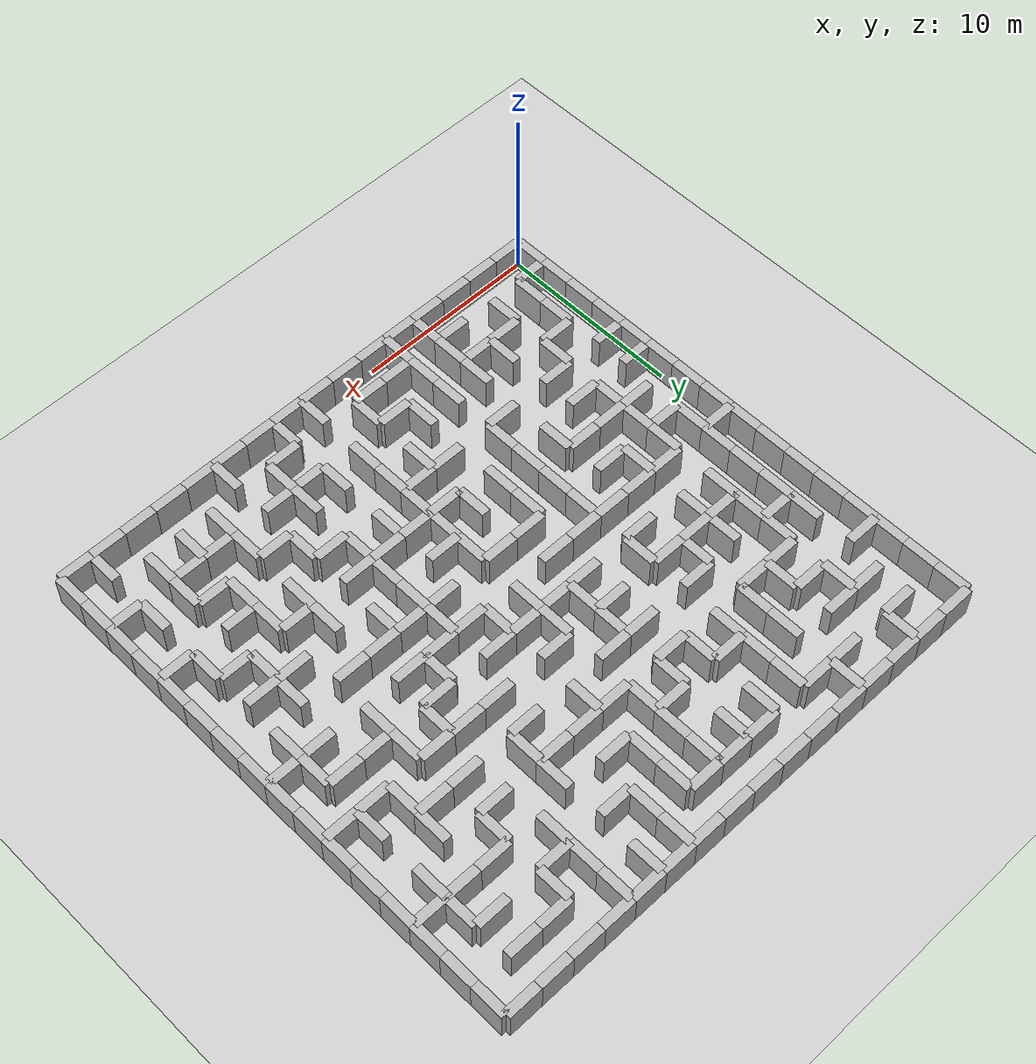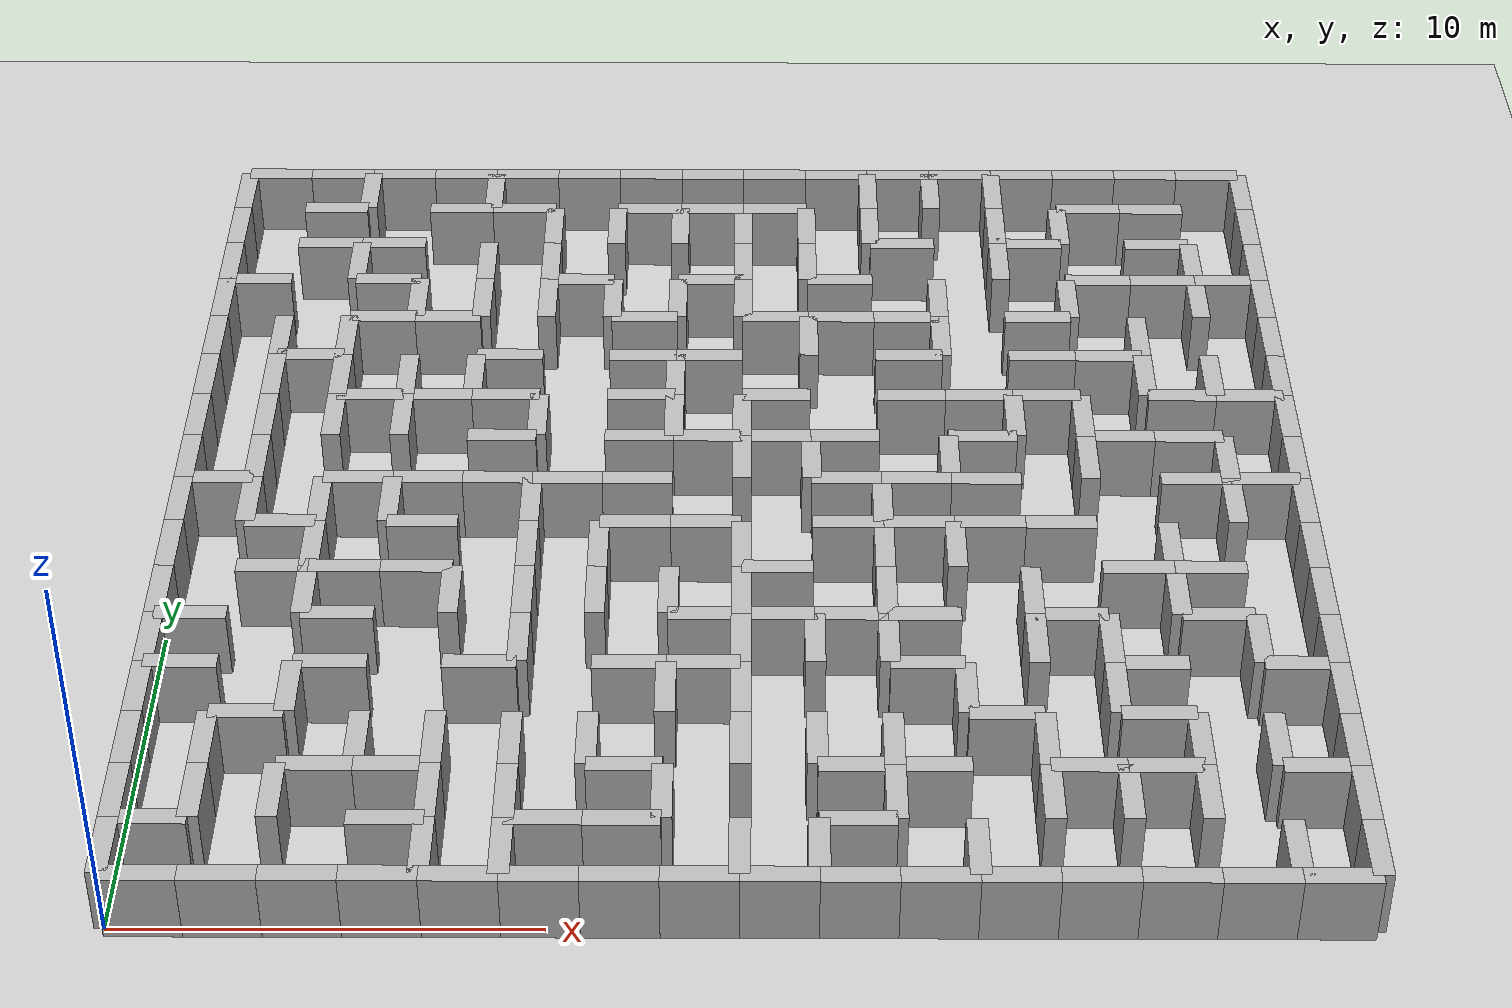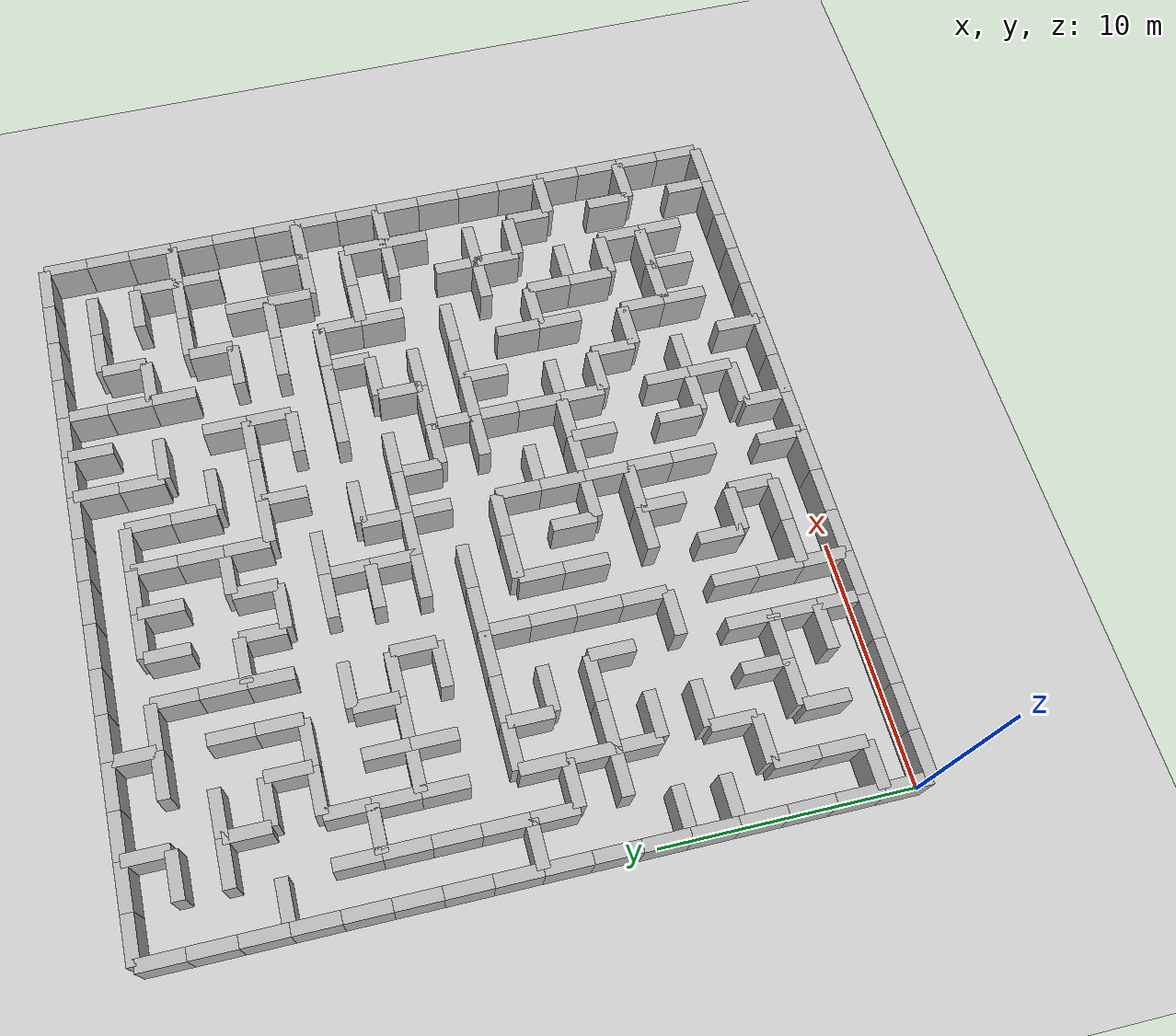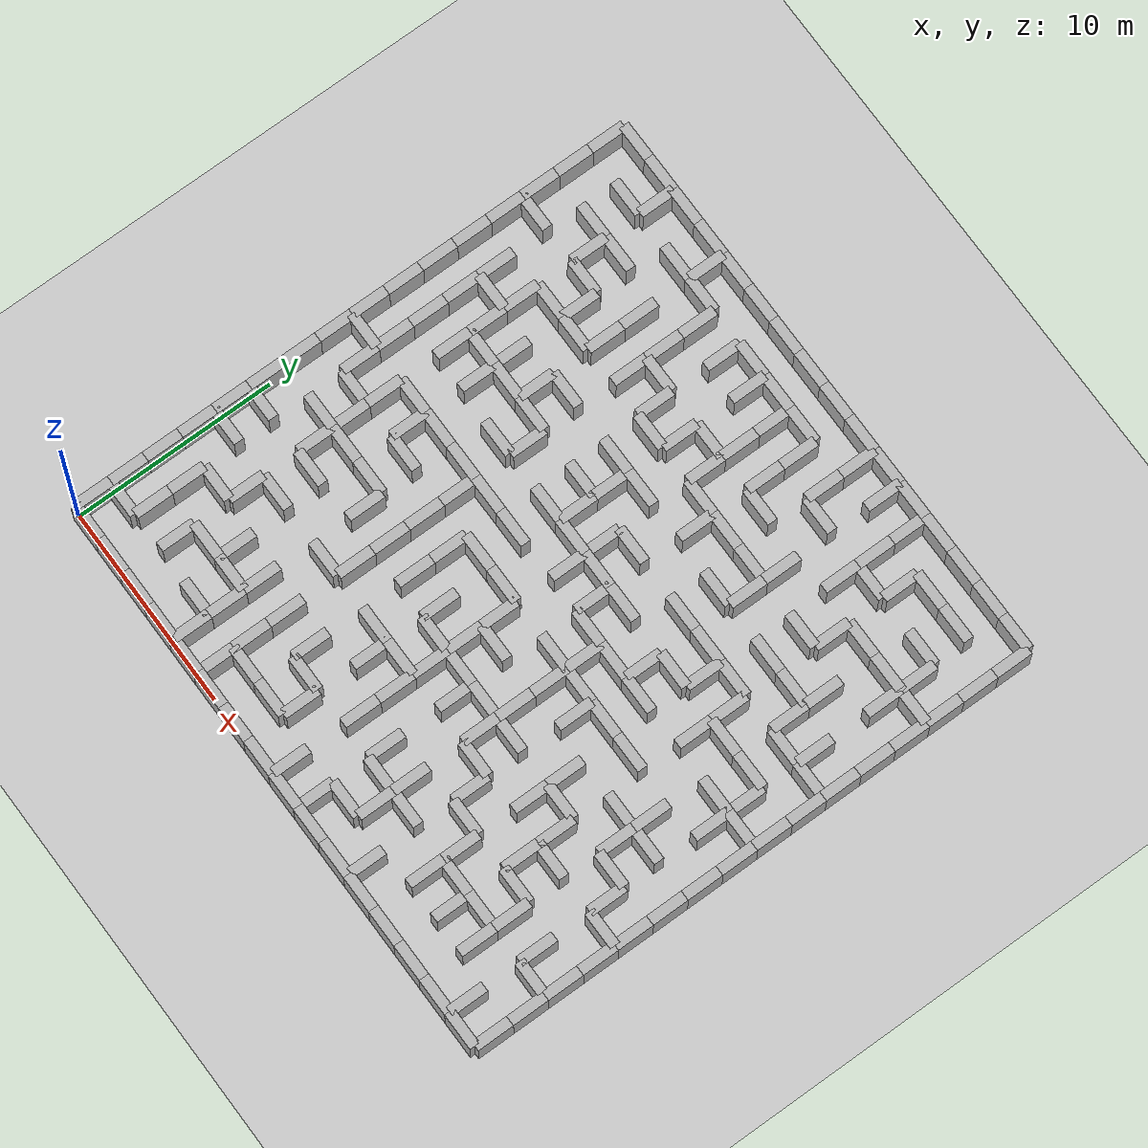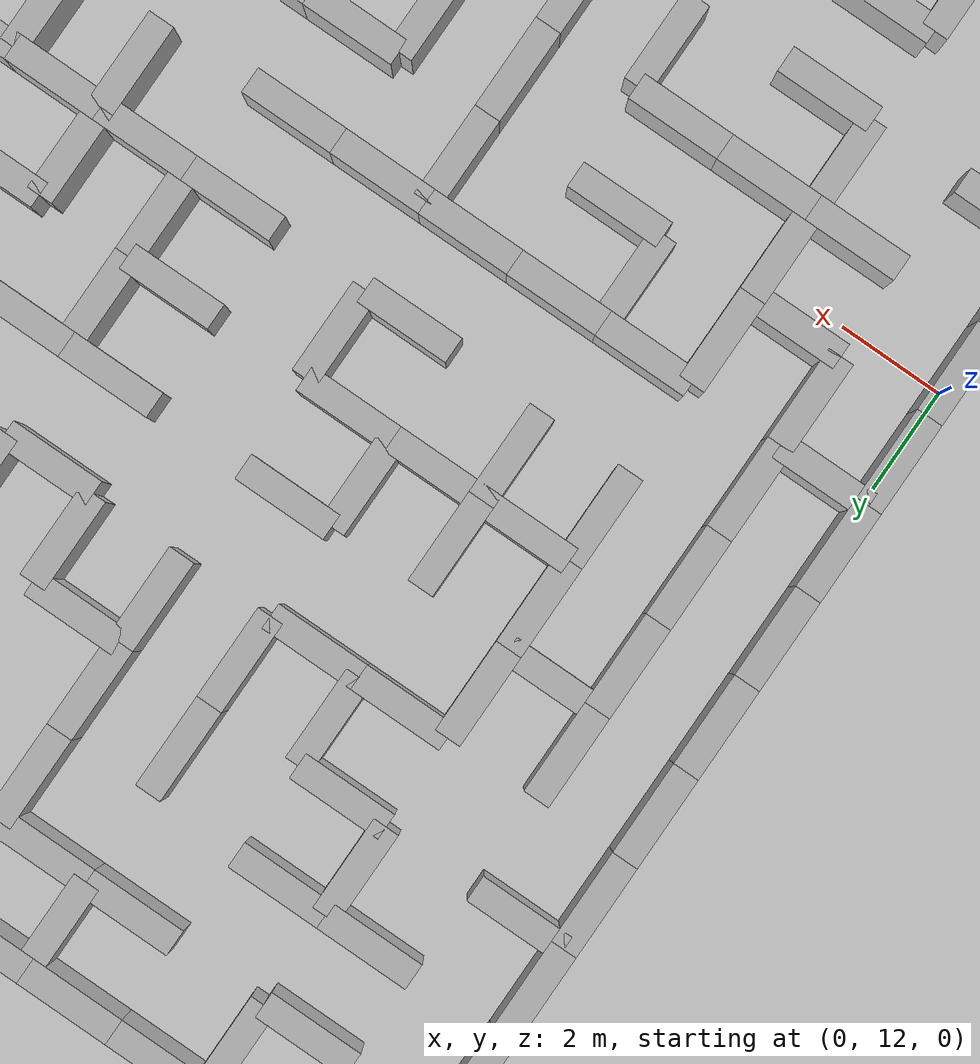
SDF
<sdf version="1.6">
 <world name="default">
  <light name="sun" type="directional">
   <pose>0 0 10 0 -0 0</pose>
   <diffuse>0.8 0.8 0.8 1</diffuse>
   <specular>0.2 0.2 0.2 1</specular>
   <attenuation>
    <range>1000</range>
    <constant>0.9</constant>
    <linear>0.01</linear>
    <quadratic>0.001</quadratic>
   </attenuation>
   <direction>-0.5 0.1 -0.9</direction>
  </light>
  <model name="ground_plane">
   <static>1</static>
   <link name="link">
    <collision name="collision">
     <geometry><plane><normal>0 0 1</normal><size>100 100</size></plane></geometry>
     <surface><friction><ode><mu>100</mu><mu2>50</mu2></ode></friction></surface>
    </collision>
    <visual name="visual">
     <cast_shadows>0</cast_shadows>
     <geometry><plane><normal>0 0 1</normal><size>100 100</size></plane></geometry>
     <material>
      <script><uri>file://media/materials/scripts/gazebo.material</uri><name>Gazebo/Grey</name></script>
     </material>
    </visual>
   </link>
  </model>
  <gravity>0 0 -9.8</gravity>
  <magnetic_field>6e-06 2.3e-05 -4.2e-05</magnetic_field>
  <atmosphere type="adiabatic"/>
  <physics name="default_physics" default="0" type="ode">
   <max_step_size>0.001</max_step_size>
   <real_time_factor>1</real_time_factor>
   <real_time_update_rate>1000</real_time_update_rate>
  </physics>
  <scene><ambient>0.4 0.4 0.4 1</ambient><background>0.7 0.7 0.7 1</background><shadows>1</shadows></scene>
  <audio><device>default</device></audio>
  <spherical_coordinates>
   <surface_model>EARTH_WGS84</surface_model>
   <latitude_deg>0</latitude_deg>
   <longitude_deg>0</longitude_deg>
   <elevation>0</elevation>
   <heading_deg>0</heading_deg>
  </spherical_coordinates>
  <model name="labyrinth_wall0">
   <pose>0.900000 0.000000 0.9 0 0 0.000000</pose>
   <link name="link">
    <inertial><mass>3.0</mass></inertial>
    <collision name="collision"><geometry><box><size>1.8 0.5 1.8</size></box></geometry></collision>
    <visual name="visual"><geometry><box><size>1.8 0.5 1.8</size></box></geometry></visual>
   </link>
   <static>true</static>
  </model>
  <model name="labyrinth_wall2">
   <pose>0.000000 0.900000 0.9 0 0 1.570796</pose>
   <link name="link">
    <inertial><mass>3.0</mass></inertial>
    <collision name="collision"><geometry><box><size>1.8 0.5 1.8</size></box></geometry></collision>
    <visual name="visual"><geometry><box><size>1.8 0.5 1.8</size></box></geometry></visual>
   </link>
   <static>true</static>
  </model>
  <model name="labyrinth_wall3">
   <pose>2.700000 0.000000 0.9 0 0 0.000000</pose>
   <link name="link">
    <inertial><mass>3.0</mass></inertial>
    <collision name="collision"><geometry><box><size>1.8 0.5 1.8</size></box></geometry></collision>
    <visual name="visual"><geometry><box><size>1.8 0.5 1.8</size></box></geometry></visual>
   </link>
   <static>true</static>
  </model>
  <model name="labyrinth_wall5">
   <pose>4.500000 0.000000 0.9 0 0 0.000000</pose>
   <link name="link">
    <inertial><mass>3.0</mass></inertial>
    <collision name="collision"><geometry><box><size>1.8 0.5 1.8</size></box></geometry></collision>
    <visual name="visual"><geometry><box><size>1.8 0.5 1.8</size></box></geometry></visual>
   </link>
   <static>true</static>
  </model>
  <model name="labyrinth_wall7">
   <pose>6.300000 0.000000 0.9 0 0 0.000000</pose>
   <link name="link">
    <inertial><mass>3.0</mass></inertial>
    <collision name="collision"><geometry><box><size>1.8 0.5 1.8</size></box></geometry></collision>
    <visual name="visual"><geometry><box><size>1.8 0.5 1.8</size></box></geometry></visual>
   </link>
   <static>true</static>
  </model>
  <model name="labyrinth_wall8">
   <pose>7.200000 0.900000 0.9 0 0 1.570796</pose>
   <link name="link">
    <inertial><mass>3.0</mass></inertial>
    <collision name="collision"><geometry><box><size>1.8 0.5 1.8</size></box></geometry></collision>
    <visual name="visual"><geometry><box><size>1.8 0.5 1.8</size></box></geometry></visual>
   </link>
   <static>true</static>
  </model>
  <model name="labyrinth_wall9">
   <pose>8.100000 0.000000 0.9 0 0 0.000000</pose>
   <link name="link">
    <inertial><mass>3.0</mass></inertial>
    <collision name="collision"><geometry><box><size>1.8 0.5 1.8</size></box></geometry></collision>
    <visual name="visual"><geometry><box><size>1.8 0.5 1.8</size></box></geometry></visual>
   </link>
   <static>true</static>
  </model>
  <model name="labyrinth_wall10">
   <pose>9.000000 0.900000 0.9 0 0 1.570796</pose>
   <link name="link">
    <inertial><mass>3.0</mass></inertial>
    <collision name="collision"><geometry><box><size>1.8 0.5 1.8</size></box></geometry></collision>
    <visual name="visual"><geometry><box><size>1.8 0.5 1.8</size></box></geometry></visual>
   </link>
   <static>true</static>
  </model>
  <model name="labyrinth_wall11">
   <pose>9.900000 0.000000 0.9 0 0 0.000000</pose>
   <link name="link">
    <inertial><mass>3.0</mass></inertial>
    <collision name="collision"><geometry><box><size>1.8 0.5 1.8</size></box></geometry></collision>
    <visual name="visual"><geometry><box><size>1.8 0.5 1.8</size></box></geometry></visual>
   </link>
   <static>true</static>
  </model>
  <model name="labyrinth_wall13">
   <pose>11.700000 0.000000 0.9 0 0 0.000000</pose>
   <link name="link">
    <inertial><mass>3.0</mass></inertial>
    <collision name="collision"><geometry><box><size>1.8 0.5 1.8</size></box></geometry></collision>
    <visual name="visual"><geometry><box><size>1.8 0.5 1.8</size></box></geometry></visual>
   </link>
   <static>true</static>
  </model>
  <model name="labyrinth_wall15">
   <pose>13.500000 0.000000 0.9 0 0 0.000000</pose>
   <link name="link">
    <inertial><mass>3.0</mass></inertial>
    <collision name="collision"><geometry><box><size>1.8 0.5 1.8</size></box></geometry></collision>
    <visual name="visual"><geometry><box><size>1.8 0.5 1.8</size></box></geometry></visual>
   </link>
   <static>true</static>
  </model>
  <model name="labyrinth_wall16">
   <pose>14.400000 0.900000 0.9 0 0 1.570796</pose>
   <link name="link">
    <inertial><mass>3.0</mass></inertial>
    <collision name="collision"><geometry><box><size>1.8 0.5 1.8</size></box></geometry></collision>
    <visual name="visual"><geometry><box><size>1.8 0.5 1.8</size></box></geometry></visual>
   </link>
   <static>true</static>
  </model>
  <model name="labyrinth_wall17">
   <pose>15.300000 0.000000 0.9 0 0 0.000000</pose>
   <link name="link">
    <inertial><mass>3.0</mass></inertial>
    <collision name="collision"><geometry><box><size>1.8 0.5 1.8</size></box></geometry></collision>
    <visual name="visual"><geometry><box><size>1.8 0.5 1.8</size></box></geometry></visual>
   </link>
   <static>true</static>
  </model>
  <model name="labyrinth_wall18">
   <pose>16.200001 0.900000 0.9 0 0 1.570796</pose>
   <link name="link">
    <inertial><mass>3.0</mass></inertial>
    <collision name="collision"><geometry><box><size>1.8 0.5 1.8</size></box></geometry></collision>
    <visual name="visual"><geometry><box><size>1.8 0.5 1.8</size></box></geometry></visual>
   </link>
   <static>true</static>
  </model>
  <model name="labyrinth_wall19">
   <pose>17.100000 0.000000 0.9 0 0 0.000000</pose>
   <link name="link">
    <inertial><mass>3.0</mass></inertial>
    <collision name="collision"><geometry><box><size>1.8 0.5 1.8</size></box></geometry></collision>
    <visual name="visual"><geometry><box><size>1.8 0.5 1.8</size></box></geometry></visual>
   </link>
   <static>true</static>
  </model>
  <model name="labyrinth_wall21">
   <pose>18.900000 0.000000 0.9 0 0 0.000000</pose>
   <link name="link">
    <inertial><mass>3.0</mass></inertial>
    <collision name="collision"><geometry><box><size>1.8 0.5 1.8</size></box></geometry></collision>
    <visual name="visual"><geometry><box><size>1.8 0.5 1.8</size></box></geometry></visual>
   </link>
   <static>true</static>
  </model>
  <model name="labyrinth_wall22">
   <pose>19.799999 0.900000 0.9 0 0 1.570796</pose>
   <link name="link">
    <inertial><mass>3.0</mass></inertial>
    <collision name="collision"><geometry><box><size>1.8 0.5 1.8</size></box></geometry></collision>
    <visual name="visual"><geometry><box><size>1.8 0.5 1.8</size></box></geometry></visual>
   </link>
   <static>true</static>
  </model>
  <model name="labyrinth_wall23">
   <pose>20.700001 0.000000 0.9 0 0 0.000000</pose>
   <link name="link">
    <inertial><mass>3.0</mass></inertial>
    <collision name="collision"><geometry><box><size>1.8 0.5 1.8</size></box></geometry></collision>
    <visual name="visual"><geometry><box><size>1.8 0.5 1.8</size></box></geometry></visual>
   </link>
   <static>true</static>
  </model>
  <model name="labyrinth_wall25">
   <pose>22.500000 0.000000 0.9 0 0 0.000000</pose>
   <link name="link">
    <inertial><mass>3.0</mass></inertial>
    <collision name="collision"><geometry><box><size>1.8 0.5 1.8</size></box></geometry></collision>
    <visual name="visual"><geometry><box><size>1.8 0.5 1.8</size></box></geometry></visual>
   </link>
   <static>true</static>
  </model>
  <model name="labyrinth_wall27">
   <pose>24.299999 0.000000 0.9 0 0 0.000000</pose>
   <link name="link">
    <inertial><mass>3.0</mass></inertial>
    <collision name="collision"><geometry><box><size>1.8 0.5 1.8</size></box></geometry></collision>
    <visual name="visual"><geometry><box><size>1.8 0.5 1.8</size></box></geometry></visual>
   </link>
   <static>true</static>
  </model>
  <model name="labyrinth_wall29">
   <pose>26.100000 0.000000 0.9 0 0 0.000000</pose>
   <link name="link">
    <inertial><mass>3.0</mass></inertial>
    <collision name="collision"><geometry><box><size>1.8 0.5 1.8</size></box></geometry></collision>
    <visual name="visual"><geometry><box><size>1.8 0.5 1.8</size></box></geometry></visual>
   </link>
   <static>true</static>
  </model>
  <model name="labyrinth_wall30">
   <pose>27.000000 0.900000 0.9 0 0 1.570796</pose>
   <link name="link">
    <inertial><mass>3.0</mass></inertial>
    <collision name="collision"><geometry><box><size>1.8 0.5 1.8</size></box></geometry></collision>
    <visual name="visual"><geometry><box><size>1.8 0.5 1.8</size></box></geometry></visual>
   </link>
   <static>true</static>
  </model>
  <model name="labyrinth_wall31">
   <pose>27.900000 0.000000 0.9 0 0 0.000000</pose>
   <link name="link">
    <inertial><mass>3.0</mass></inertial>
    <collision name="collision"><geometry><box><size>1.8 0.5 1.8</size></box></geometry></collision>
    <visual name="visual"><geometry><box><size>1.8 0.5 1.8</size></box></geometry></visual>
   </link>
   <static>true</static>
  </model>
  <model name="labyrinth_wall32">
   <pose>28.799999 0.900000 0.9 0 0 1.570796</pose>
   <link name="link">
    <inertial><mass>3.0</mass></inertial>
    <collision name="collision"><geometry><box><size>1.8 0.5 1.8</size></box></geometry></collision>
    <visual name="visual"><geometry><box><size>1.8 0.5 1.8</size></box></geometry></visual>
   </link>
   <static>true</static>
  </model>
  <model name="labyrinth_wall33">
   <pose>0.900000 1.800000 0.9 0 0 0.000000</pose>
   <link name="link">
    <inertial><mass>3.0</mass></inertial>
    <collision name="collision"><geometry><box><size>1.8 0.5 1.8</size></box></geometry></collision>
    <visual name="visual"><geometry><box><size>1.8 0.5 1.8</size></box></geometry></visual>
   </link>
   <static>true</static>
  </model>
  <model name="labyrinth_wall34">
   <pose>1.800000 2.700000 0.9 0 0 1.570796</pose>
   <link name="link">
    <inertial><mass>3.0</mass></inertial>
    <collision name="collision"><geometry><box><size>1.8 0.5 1.8</size></box></geometry></collision>
    <visual name="visual"><geometry><box><size>1.8 0.5 1.8</size></box></geometry></visual>
   </link>
   <static>true</static>
  </model>
  <model name="labyrinth_wall35">
   <pose>0.000000 2.700000 0.9 0 0 1.570796</pose>
   <link name="link">
    <inertial><mass>3.0</mass></inertial>
    <collision name="collision"><geometry><box><size>1.8 0.5 1.8</size></box></geometry></collision>
    <visual name="visual"><geometry><box><size>1.8 0.5 1.8</size></box></geometry></visual>
   </link>
   <static>true</static>
  </model>
  <model name="labyrinth_wall37">
   <pose>3.600000 2.700000 0.9 0 0 1.570796</pose>
   <link name="link">
    <inertial><mass>3.0</mass></inertial>
    <collision name="collision"><geometry><box><size>1.8 0.5 1.8</size></box></geometry></collision>
    <visual name="visual"><geometry><box><size>1.8 0.5 1.8</size></box></geometry></visual>
   </link>
   <static>true</static>
  </model>
  <model name="labyrinth_wall40">
   <pose>6.300000 1.800000 0.9 0 0 0.000000</pose>
   <link name="link">
    <inertial><mass>3.0</mass></inertial>
    <collision name="collision"><geometry><box><size>1.8 0.5 1.8</size></box></geometry></collision>
    <visual name="visual"><geometry><box><size>1.8 0.5 1.8</size></box></geometry></visual>
   </link>
   <static>true</static>
  </model>
  <model name="labyrinth_wall41">
   <pose>7.200000 2.700000 0.9 0 0 1.570796</pose>
   <link name="link">
    <inertial><mass>3.0</mass></inertial>
    <collision name="collision"><geometry><box><size>1.8 0.5 1.8</size></box></geometry></collision>
    <visual name="visual"><geometry><box><size>1.8 0.5 1.8</size></box></geometry></visual>
   </link>
   <static>true</static>
  </model>
  <model name="labyrinth_wall43">
   <pose>9.000000 2.700000 0.9 0 0 1.570796</pose>
   <link name="link">
    <inertial><mass>3.0</mass></inertial>
    <collision name="collision"><geometry><box><size>1.8 0.5 1.8</size></box></geometry></collision>
    <visual name="visual"><geometry><box><size>1.8 0.5 1.8</size></box></geometry></visual>
   </link>
   <static>true</static>
  </model>
  <model name="labyrinth_wall44">
   <pose>9.900000 1.800000 0.9 0 0 0.000000</pose>
   <link name="link">
    <inertial><mass>3.0</mass></inertial>
    <collision name="collision"><geometry><box><size>1.8 0.5 1.8</size></box></geometry></collision>
    <visual name="visual"><geometry><box><size>1.8 0.5 1.8</size></box></geometry></visual>
   </link>
   <static>true</static>
  </model>
  <model name="labyrinth_wall46">
   <pose>11.700000 1.800000 0.9 0 0 0.000000</pose>
   <link name="link">
    <inertial><mass>3.0</mass></inertial>
    <collision name="collision"><geometry><box><size>1.8 0.5 1.8</size></box></geometry></collision>
    <visual name="visual"><geometry><box><size>1.8 0.5 1.8</size></box></geometry></visual>
   </link>
   <static>true</static>
  </model>
  <model name="labyrinth_wall47">
   <pose>12.600000 2.700000 0.9 0 0 1.570796</pose>
   <link name="link">
    <inertial><mass>3.0</mass></inertial>
    <collision name="collision"><geometry><box><size>1.8 0.5 1.8</size></box></geometry></collision>
    <visual name="visual"><geometry><box><size>1.8 0.5 1.8</size></box></geometry></visual>
   </link>
   <static>true</static>
  </model>
  <model name="labyrinth_wall52">
   <pose>17.100000 1.800000 0.9 0 0 0.000000</pose>
   <link name="link">
    <inertial><mass>3.0</mass></inertial>
    <collision name="collision"><geometry><box><size>1.8 0.5 1.8</size></box></geometry></collision>
    <visual name="visual"><geometry><box><size>1.8 0.5 1.8</size></box></geometry></visual>
   </link>
   <static>true</static>
  </model>
  <model name="labyrinth_wall53">
   <pose>18.000000 2.700000 0.9 0 0 1.570796</pose>
   <link name="link">
    <inertial><mass>3.0</mass></inertial>
    <collision name="collision"><geometry><box><size>1.8 0.5 1.8</size></box></geometry></collision>
    <visual name="visual"><geometry><box><size>1.8 0.5 1.8</size></box></geometry></visual>
   </link>
   <static>true</static>
  </model>
  <model name="labyrinth_wall57">
   <pose>21.600000 2.700000 0.9 0 0 1.570796</pose>
   <link name="link">
    <inertial><mass>3.0</mass></inertial>
    <collision name="collision"><geometry><box><size>1.8 0.5 1.8</size></box></geometry></collision>
    <visual name="visual"><geometry><box><size>1.8 0.5 1.8</size></box></geometry></visual>
   </link>
   <static>true</static>
  </model>
  <model name="labyrinth_wall59">
   <pose>23.400000 2.700000 0.9 0 0 1.570796</pose>
   <link name="link">
    <inertial><mass>3.0</mass></inertial>
    <collision name="collision"><geometry><box><size>1.8 0.5 1.8</size></box></geometry></collision>
    <visual name="visual"><geometry><box><size>1.8 0.5 1.8</size></box></geometry></visual>
   </link>
   <static>true</static>
  </model>
  <model name="labyrinth_wall61">
   <pose>25.200001 2.700000 0.9 0 0 1.570796</pose>
   <link name="link">
    <inertial><mass>3.0</mass></inertial>
    <collision name="collision"><geometry><box><size>1.8 0.5 1.8</size></box></geometry></collision>
    <visual name="visual"><geometry><box><size>1.8 0.5 1.8</size></box></geometry></visual>
   </link>
   <static>true</static>
  </model>
  <model name="labyrinth_wall65">
   <pose>28.799999 2.700000 0.9 0 0 1.570796</pose>
   <link name="link">
    <inertial><mass>3.0</mass></inertial>
    <collision name="collision"><geometry><box><size>1.8 0.5 1.8</size></box></geometry></collision>
    <visual name="visual"><geometry><box><size>1.8 0.5 1.8</size></box></geometry></visual>
   </link>
   <static>true</static>
  </model>
  <model name="labyrinth_wall67">
   <pose>1.800000 4.500000 0.9 0 0 1.570796</pose>
   <link name="link">
    <inertial><mass>3.0</mass></inertial>
    <collision name="collision"><geometry><box><size>1.8 0.5 1.8</size></box></geometry></collision>
    <visual name="visual"><geometry><box><size>1.8 0.5 1.8</size></box></geometry></visual>
   </link>
   <static>true</static>
  </model>
  <model name="labyrinth_wall68">
   <pose>0.000000 4.500000 0.9 0 0 1.570796</pose>
   <link name="link">
    <inertial><mass>3.0</mass></inertial>
    <collision name="collision"><geometry><box><size>1.8 0.5 1.8</size></box></geometry></collision>
    <visual name="visual"><geometry><box><size>1.8 0.5 1.8</size></box></geometry></visual>
   </link>
   <static>true</static>
  </model>
  <model name="labyrinth_wall71">
   <pose>4.500000 3.600000 0.9 0 0 0.000000</pose>
   <link name="link">
    <inertial><mass>3.0</mass></inertial>
    <collision name="collision"><geometry><box><size>1.8 0.5 1.8</size></box></geometry></collision>
    <visual name="visual"><geometry><box><size>1.8 0.5 1.8</size></box></geometry></visual>
   </link>
   <static>true</static>
  </model>
  <model name="labyrinth_wall72">
   <pose>5.400000 4.500000 0.9 0 0 1.570796</pose>
   <link name="link">
    <inertial><mass>3.0</mass></inertial>
    <collision name="collision"><geometry><box><size>1.8 0.5 1.8</size></box></geometry></collision>
    <visual name="visual"><geometry><box><size>1.8 0.5 1.8</size></box></geometry></visual>
   </link>
   <static>true</static>
  </model>
  <model name="labyrinth_wall73">
   <pose>6.300000 3.600000 0.9 0 0 0.000000</pose>
   <link name="link">
    <inertial><mass>3.0</mass></inertial>
    <collision name="collision"><geometry><box><size>1.8 0.5 1.8</size></box></geometry></collision>
    <visual name="visual"><geometry><box><size>1.8 0.5 1.8</size></box></geometry></visual>
   </link>
   <static>true</static>
  </model>
  <model name="labyrinth_wall74">
   <pose>7.200000 4.500000 0.9 0 0 1.570796</pose>
   <link name="link">
    <inertial><mass>3.0</mass></inertial>
    <collision name="collision"><geometry><box><size>1.8 0.5 1.8</size></box></geometry></collision>
    <visual name="visual"><geometry><box><size>1.8 0.5 1.8</size></box></geometry></visual>
   </link>
   <static>true</static>
  </model>
  <model name="labyrinth_wall76">
   <pose>9.000000 4.500000 0.9 0 0 1.570796</pose>
   <link name="link">
    <inertial><mass>3.0</mass></inertial>
    <collision name="collision"><geometry><box><size>1.8 0.5 1.8</size></box></geometry></collision>
    <visual name="visual"><geometry><box><size>1.8 0.5 1.8</size></box></geometry></visual>
   </link>
   <static>true</static>
  </model>
  <model name="labyrinth_wall78">
   <pose>10.800000 4.500000 0.9 0 0 1.570796</pose>
   <link name="link">
    <inertial><mass>3.0</mass></inertial>
    <collision name="collision"><geometry><box><size>1.8 0.5 1.8</size></box></geometry></collision>
    <visual name="visual"><geometry><box><size>1.8 0.5 1.8</size></box></geometry></visual>
   </link>
   <static>true</static>
  </model>
  <model name="labyrinth_wall79">
   <pose>11.700000 3.600000 0.9 0 0 0.000000</pose>
   <link name="link">
    <inertial><mass>3.0</mass></inertial>
    <collision name="collision"><geometry><box><size>1.8 0.5 1.8</size></box></geometry></collision>
    <visual name="visual"><geometry><box><size>1.8 0.5 1.8</size></box></geometry></visual>
   </link>
   <static>true</static>
  </model>
  <model name="labyrinth_wall82">
   <pose>14.400000 4.500000 0.9 0 0 1.570796</pose>
   <link name="link">
    <inertial><mass>3.0</mass></inertial>
    <collision name="collision"><geometry><box><size>1.8 0.5 1.8</size></box></geometry></collision>
    <visual name="visual"><geometry><box><size>1.8 0.5 1.8</size></box></geometry></visual>
   </link>
   <static>true</static>
  </model>
  <model name="labyrinth_wall84">
   <pose>16.200001 4.500000 0.9 0 0 1.570796</pose>
   <link name="link">
    <inertial><mass>3.0</mass></inertial>
    <collision name="collision"><geometry><box><size>1.8 0.5 1.8</size></box></geometry></collision>
    <visual name="visual"><geometry><box><size>1.8 0.5 1.8</size></box></geometry></visual>
   </link>
   <static>true</static>
  </model>
  <model name="labyrinth_wall85">
   <pose>17.100000 3.600000 0.9 0 0 0.000000</pose>
   <link name="link">
    <inertial><mass>3.0</mass></inertial>
    <collision name="collision"><geometry><box><size>1.8 0.5 1.8</size></box></geometry></collision>
    <visual name="visual"><geometry><box><size>1.8 0.5 1.8</size></box></geometry></visual>
   </link>
   <static>true</static>
  </model>
  <model name="labyrinth_wall86">
   <pose>18.000000 4.500000 0.9 0 0 1.570796</pose>
   <link name="link">
    <inertial><mass>3.0</mass></inertial>
    <collision name="collision"><geometry><box><size>1.8 0.5 1.8</size></box></geometry></collision>
    <visual name="visual"><geometry><box><size>1.8 0.5 1.8</size></box></geometry></visual>
   </link>
   <static>true</static>
  </model>
  <model name="labyrinth_wall87">
   <pose>18.900000 3.600000 0.9 0 0 0.000000</pose>
   <link name="link">
    <inertial><mass>3.0</mass></inertial>
    <collision name="collision"><geometry><box><size>1.8 0.5 1.8</size></box></geometry></collision>
    <visual name="visual"><geometry><box><size>1.8 0.5 1.8</size></box></geometry></visual>
   </link>
   <static>true</static>
  </model>
  <model name="labyrinth_wall90">
   <pose>21.600000 4.500000 0.9 0 0 1.570796</pose>
   <link name="link">
    <inertial><mass>3.0</mass></inertial>
    <collision name="collision"><geometry><box><size>1.8 0.5 1.8</size></box></geometry></collision>
    <visual name="visual"><geometry><box><size>1.8 0.5 1.8</size></box></geometry></visual>
   </link>
   <static>true</static>
  </model>
  <model name="labyrinth_wall91">
   <pose>22.500000 3.600000 0.9 0 0 0.000000</pose>
   <link name="link">
    <inertial><mass>3.0</mass></inertial>
    <collision name="collision"><geometry><box><size>1.8 0.5 1.8</size></box></geometry></collision>
    <visual name="visual"><geometry><box><size>1.8 0.5 1.8</size></box></geometry></visual>
   </link>
   <static>true</static>
  </model>
  <model name="labyrinth_wall93">
   <pose>24.299999 3.600000 0.9 0 0 0.000000</pose>
   <link name="link">
    <inertial><mass>3.0</mass></inertial>
    <collision name="collision"><geometry><box><size>1.8 0.5 1.8</size></box></geometry></collision>
    <visual name="visual"><geometry><box><size>1.8 0.5 1.8</size></box></geometry></visual>
   </link>
   <static>true</static>
  </model>
  <model name="labyrinth_wall94">
   <pose>25.200001 4.500000 0.9 0 0 1.570796</pose>
   <link name="link">
    <inertial><mass>3.0</mass></inertial>
    <collision name="collision"><geometry><box><size>1.8 0.5 1.8</size></box></geometry></collision>
    <visual name="visual"><geometry><box><size>1.8 0.5 1.8</size></box></geometry></visual>
   </link>
   <static>true</static>
  </model>
  <model name="labyrinth_wall96">
   <pose>27.000000 4.500000 0.9 0 0 1.570796</pose>
   <link name="link">
    <inertial><mass>3.0</mass></inertial>
    <collision name="collision"><geometry><box><size>1.8 0.5 1.8</size></box></geometry></collision>
    <visual name="visual"><geometry><box><size>1.8 0.5 1.8</size></box></geometry></visual>
   </link>
   <static>true</static>
  </model>
  <model name="labyrinth_wall97">
   <pose>27.900000 3.600000 0.9 0 0 0.000000</pose>
   <link name="link">
    <inertial><mass>3.0</mass></inertial>
    <collision name="collision"><geometry><box><size>1.8 0.5 1.8</size></box></geometry></collision>
    <visual name="visual"><geometry><box><size>1.8 0.5 1.8</size></box></geometry></visual>
   </link>
   <static>true</static>
  </model>
  <model name="labyrinth_wall98">
   <pose>28.799999 4.500000 0.9 0 0 1.570796</pose>
   <link name="link">
    <inertial><mass>3.0</mass></inertial>
    <collision name="collision"><geometry><box><size>1.8 0.5 1.8</size></box></geometry></collision>
    <visual name="visual"><geometry><box><size>1.8 0.5 1.8</size></box></geometry></visual>
   </link>
   <static>true</static>
  </model>
  <model name="labyrinth_wall101">
   <pose>0.000000 6.300000 0.9 0 0 1.570796</pose>
   <link name="link">
    <inertial><mass>3.0</mass></inertial>
    <collision name="collision"><geometry><box><size>1.8 0.5 1.8</size></box></geometry></collision>
    <visual name="visual"><geometry><box><size>1.8 0.5 1.8</size></box></geometry></visual>
   </link>
   <static>true</static>
  </model>
  <model name="labyrinth_wall102">
   <pose>2.700000 5.400000 0.9 0 0 0.000000</pose>
   <link name="link">
    <inertial><mass>3.0</mass></inertial>
    <collision name="collision"><geometry><box><size>1.8 0.5 1.8</size></box></geometry></collision>
    <visual name="visual"><geometry><box><size>1.8 0.5 1.8</size></box></geometry></visual>
   </link>
   <static>true</static>
  </model>
  <model name="labyrinth_wall103">
   <pose>3.600000 6.300000 0.9 0 0 1.570796</pose>
   <link name="link">
    <inertial><mass>3.0</mass></inertial>
    <collision name="collision"><geometry><box><size>1.8 0.5 1.8</size></box></geometry></collision>
    <visual name="visual"><geometry><box><size>1.8 0.5 1.8</size></box></geometry></visual>
   </link>
   <static>true</static>
  </model>
  <model name="labyrinth_wall113">
   <pose>12.600000 6.300000 0.9 0 0 1.570796</pose>
   <link name="link">
    <inertial><mass>3.0</mass></inertial>
    <collision name="collision"><geometry><box><size>1.8 0.5 1.8</size></box></geometry></collision>
    <visual name="visual"><geometry><box><size>1.8 0.5 1.8</size></box></geometry></visual>
   </link>
   <static>true</static>
  </model>
  <model name="labyrinth_wall115">
   <pose>14.400000 6.300000 0.9 0 0 1.570796</pose>
   <link name="link">
    <inertial><mass>3.0</mass></inertial>
    <collision name="collision"><geometry><box><size>1.8 0.5 1.8</size></box></geometry></collision>
    <visual name="visual"><geometry><box><size>1.8 0.5 1.8</size></box></geometry></visual>
   </link>
   <static>true</static>
  </model>
  <model name="labyrinth_wall121">
   <pose>19.799999 6.300000 0.9 0 0 1.570796</pose>
   <link name="link">
    <inertial><mass>3.0</mass></inertial>
    <collision name="collision"><geometry><box><size>1.8 0.5 1.8</size></box></geometry></collision>
    <visual name="visual"><geometry><box><size>1.8 0.5 1.8</size></box></geometry></visual>
   </link>
   <static>true</static>
  </model>
  <model name="labyrinth_wall122">
   <pose>20.700001 5.400000 0.9 0 0 0.000000</pose>
   <link name="link">
    <inertial><mass>3.0</mass></inertial>
    <collision name="collision"><geometry><box><size>1.8 0.5 1.8</size></box></geometry></collision>
    <visual name="visual"><geometry><box><size>1.8 0.5 1.8</size></box></geometry></visual>
   </link>
   <static>true</static>
  </model>
  <model name="labyrinth_wall125">
   <pose>23.400000 6.300000 0.9 0 0 1.570796</pose>
   <link name="link">
    <inertial><mass>3.0</mass></inertial>
    <collision name="collision"><geometry><box><size>1.8 0.5 1.8</size></box></geometry></collision>
    <visual name="visual"><geometry><box><size>1.8 0.5 1.8</size></box></geometry></visual>
   </link>
   <static>true</static>
  </model>
  <model name="labyrinth_wall126">
   <pose>24.299999 5.400000 0.9 0 0 0.000000</pose>
   <link name="link">
    <inertial><mass>3.0</mass></inertial>
    <collision name="collision"><geometry><box><size>1.8 0.5 1.8</size></box></geometry></collision>
    <visual name="visual"><geometry><box><size>1.8 0.5 1.8</size></box></geometry></visual>
   </link>
   <static>true</static>
  </model>
  <model name="labyrinth_wall131">
   <pose>28.799999 6.300000 0.9 0 0 1.570796</pose>
   <link name="link">
    <inertial><mass>3.0</mass></inertial>
    <collision name="collision"><geometry><box><size>1.8 0.5 1.8</size></box></geometry></collision>
    <visual name="visual"><geometry><box><size>1.8 0.5 1.8</size></box></geometry></visual>
   </link>
   <static>true</static>
  </model>
  <model name="labyrinth_wall132">
   <pose>0.900000 7.200000 0.9 0 0 0.000000</pose>
   <link name="link">
    <inertial><mass>3.0</mass></inertial>
    <collision name="collision"><geometry><box><size>1.8 0.5 1.8</size></box></geometry></collision>
    <visual name="visual"><geometry><box><size>1.8 0.5 1.8</size></box></geometry></visual>
   </link>
   <static>true</static>
  </model>
  <model name="labyrinth_wall134">
   <pose>0.000000 8.100000 0.9 0 0 1.570796</pose>
   <link name="link">
    <inertial><mass>3.0</mass></inertial>
    <collision name="collision"><geometry><box><size>1.8 0.5 1.8</size></box></geometry></collision>
    <visual name="visual"><geometry><box><size>1.8 0.5 1.8</size></box></geometry></visual>
   </link>
   <static>true</static>
  </model>
  <model name="labyrinth_wall137">
   <pose>4.500000 7.200000 0.9 0 0 0.000000</pose>
   <link name="link">
    <inertial><mass>3.0</mass></inertial>
    <collision name="collision"><geometry><box><size>1.8 0.5 1.8</size></box></geometry></collision>
    <visual name="visual"><geometry><box><size>1.8 0.5 1.8</size></box></geometry></visual>
   </link>
   <static>true</static>
  </model>
  <model name="labyrinth_wall141">
   <pose>8.100000 7.200000 0.9 0 0 0.000000</pose>
   <link name="link">
    <inertial><mass>3.0</mass></inertial>
    <collision name="collision"><geometry><box><size>1.8 0.5 1.8</size></box></geometry></collision>
    <visual name="visual"><geometry><box><size>1.8 0.5 1.8</size></box></geometry></visual>
   </link>
   <static>true</static>
  </model>
  <model name="labyrinth_wall142">
   <pose>9.000000 8.100000 0.9 0 0 1.570796</pose>
   <link name="link">
    <inertial><mass>3.0</mass></inertial>
    <collision name="collision"><geometry><box><size>1.8 0.5 1.8</size></box></geometry></collision>
    <visual name="visual"><geometry><box><size>1.8 0.5 1.8</size></box></geometry></visual>
   </link>
   <static>true</static>
  </model>
  <model name="labyrinth_wall145">
   <pose>11.700000 7.200000 0.9 0 0 0.000000</pose>
   <link name="link">
    <inertial><mass>3.0</mass></inertial>
    <collision name="collision"><geometry><box><size>1.8 0.5 1.8</size></box></geometry></collision>
    <visual name="visual"><geometry><box><size>1.8 0.5 1.8</size></box></geometry></visual>
   </link>
   <static>true</static>
  </model>
  <model name="labyrinth_wall147">
   <pose>13.500000 7.200000 0.9 0 0 0.000000</pose>
   <link name="link">
    <inertial><mass>3.0</mass></inertial>
    <collision name="collision"><geometry><box><size>1.8 0.5 1.8</size></box></geometry></collision>
    <visual name="visual"><geometry><box><size>1.8 0.5 1.8</size></box></geometry></visual>
   </link>
   <static>true</static>
  </model>
  <model name="labyrinth_wall148">
   <pose>14.400000 8.100000 0.9 0 0 1.570796</pose>
   <link name="link">
    <inertial><mass>3.0</mass></inertial>
    <collision name="collision"><geometry><box><size>1.8 0.5 1.8</size></box></geometry></collision>
    <visual name="visual"><geometry><box><size>1.8 0.5 1.8</size></box></geometry></visual>
   </link>
   <static>true</static>
  </model>
  <model name="labyrinth_wall150">
   <pose>16.200001 8.100000 0.9 0 0 1.570796</pose>
   <link name="link">
    <inertial><mass>3.0</mass></inertial>
    <collision name="collision"><geometry><box><size>1.8 0.5 1.8</size></box></geometry></collision>
    <visual name="visual"><geometry><box><size>1.8 0.5 1.8</size></box></geometry></visual>
   </link>
   <static>true</static>
  </model>
  <model name="labyrinth_wall152">
   <pose>18.000000 8.100000 0.9 0 0 1.570796</pose>
   <link name="link">
    <inertial><mass>3.0</mass></inertial>
    <collision name="collision"><geometry><box><size>1.8 0.5 1.8</size></box></geometry></collision>
    <visual name="visual"><geometry><box><size>1.8 0.5 1.8</size></box></geometry></visual>
   </link>
   <static>true</static>
  </model>
  <model name="labyrinth_wall153">
   <pose>18.900000 7.200000 0.9 0 0 0.000000</pose>
   <link name="link">
    <inertial><mass>3.0</mass></inertial>
    <collision name="collision"><geometry><box><size>1.8 0.5 1.8</size></box></geometry></collision>
    <visual name="visual"><geometry><box><size>1.8 0.5 1.8</size></box></geometry></visual>
   </link>
   <static>true</static>
  </model>
  <model name="labyrinth_wall156">
   <pose>21.600000 8.100000 0.9 0 0 1.570796</pose>
   <link name="link">
    <inertial><mass>3.0</mass></inertial>
    <collision name="collision"><geometry><box><size>1.8 0.5 1.8</size></box></geometry></collision>
    <visual name="visual"><geometry><box><size>1.8 0.5 1.8</size></box></geometry></visual>
   </link>
   <static>true</static>
  </model>
  <model name="labyrinth_wall158">
   <pose>23.400000 8.100000 0.9 0 0 1.570796</pose>
   <link name="link">
    <inertial><mass>3.0</mass></inertial>
    <collision name="collision"><geometry><box><size>1.8 0.5 1.8</size></box></geometry></collision>
    <visual name="visual"><geometry><box><size>1.8 0.5 1.8</size></box></geometry></visual>
   </link>
   <static>true</static>
  </model>
  <model name="labyrinth_wall159">
   <pose>24.299999 7.200000 0.9 0 0 0.000000</pose>
   <link name="link">
    <inertial><mass>3.0</mass></inertial>
    <collision name="collision"><geometry><box><size>1.8 0.5 1.8</size></box></geometry></collision>
    <visual name="visual"><geometry><box><size>1.8 0.5 1.8</size></box></geometry></visual>
   </link>
   <static>true</static>
  </model>
  <model name="labyrinth_wall162">
   <pose>27.000000 8.100000 0.9 0 0 1.570796</pose>
   <link name="link">
    <inertial><mass>3.0</mass></inertial>
    <collision name="collision"><geometry><box><size>1.8 0.5 1.8</size></box></geometry></collision>
    <visual name="visual"><geometry><box><size>1.8 0.5 1.8</size></box></geometry></visual>
   </link>
   <static>true</static>
  </model>
  <model name="labyrinth_wall163">
   <pose>27.900000 7.200000 0.9 0 0 0.000000</pose>
   <link name="link">
    <inertial><mass>3.0</mass></inertial>
    <collision name="collision"><geometry><box><size>1.8 0.5 1.8</size></box></geometry></collision>
    <visual name="visual"><geometry><box><size>1.8 0.5 1.8</size></box></geometry></visual>
   </link>
   <static>true</static>
  </model>
  <model name="labyrinth_wall164">
   <pose>28.799999 8.100000 0.9 0 0 1.570796</pose>
   <link name="link">
    <inertial><mass>3.0</mass></inertial>
    <collision name="collision"><geometry><box><size>1.8 0.5 1.8</size></box></geometry></collision>
    <visual name="visual"><geometry><box><size>1.8 0.5 1.8</size></box></geometry></visual>
   </link>
   <static>true</static>
  </model>
  <model name="labyrinth_wall165">
   <pose>0.900000 9.000000 0.9 0 0 0.000000</pose>
   <link name="link">
    <inertial><mass>3.0</mass></inertial>
    <collision name="collision"><geometry><box><size>1.8 0.5 1.8</size></box></geometry></collision>
    <visual name="visual"><geometry><box><size>1.8 0.5 1.8</size></box></geometry></visual>
   </link>
   <static>true</static>
  </model>
  <model name="labyrinth_wall167">
   <pose>0.000000 9.900000 0.9 0 0 1.570796</pose>
   <link name="link">
    <inertial><mass>3.0</mass></inertial>
    <collision name="collision"><geometry><box><size>1.8 0.5 1.8</size></box></geometry></collision>
    <visual name="visual"><geometry><box><size>1.8 0.5 1.8</size></box></geometry></visual>
   </link>
   <static>true</static>
  </model>
  <model name="labyrinth_wall169">
   <pose>3.600000 9.900000 0.9 0 0 1.570796</pose>
   <link name="link">
    <inertial><mass>3.0</mass></inertial>
    <collision name="collision"><geometry><box><size>1.8 0.5 1.8</size></box></geometry></collision>
    <visual name="visual"><geometry><box><size>1.8 0.5 1.8</size></box></geometry></visual>
   </link>
   <static>true</static>
  </model>
  <model name="labyrinth_wall170">
   <pose>4.500000 9.000000 0.9 0 0 0.000000</pose>
   <link name="link">
    <inertial><mass>3.0</mass></inertial>
    <collision name="collision"><geometry><box><size>1.8 0.5 1.8</size></box></geometry></collision>
    <visual name="visual"><geometry><box><size>1.8 0.5 1.8</size></box></geometry></visual>
   </link>
   <static>true</static>
  </model>
  <model name="labyrinth_wall173">
   <pose>7.200000 9.900000 0.9 0 0 1.570796</pose>
   <link name="link">
    <inertial><mass>3.0</mass></inertial>
    <collision name="collision"><geometry><box><size>1.8 0.5 1.8</size></box></geometry></collision>
    <visual name="visual"><geometry><box><size>1.8 0.5 1.8</size></box></geometry></visual>
   </link>
   <static>true</static>
  </model>
  <model name="labyrinth_wall175">
   <pose>9.000000 9.900000 0.9 0 0 1.570796</pose>
   <link name="link">
    <inertial><mass>3.0</mass></inertial>
    <collision name="collision"><geometry><box><size>1.8 0.5 1.8</size></box></geometry></collision>
    <visual name="visual"><geometry><box><size>1.8 0.5 1.8</size></box></geometry></visual>
   </link>
   <static>true</static>
  </model>
  <model name="labyrinth_wall177">
   <pose>10.800000 9.900000 0.9 0 0 1.570796</pose>
   <link name="link">
    <inertial><mass>3.0</mass></inertial>
    <collision name="collision"><geometry><box><size>1.8 0.5 1.8</size></box></geometry></collision>
    <visual name="visual"><geometry><box><size>1.8 0.5 1.8</size></box></geometry></visual>
   </link>
   <static>true</static>
  </model>
  <model name="labyrinth_wall179">
   <pose>12.600000 9.900000 0.9 0 0 1.570796</pose>
   <link name="link">
    <inertial><mass>3.0</mass></inertial>
    <collision name="collision"><geometry><box><size>1.8 0.5 1.8</size></box></geometry></collision>
    <visual name="visual"><geometry><box><size>1.8 0.5 1.8</size></box></geometry></visual>
   </link>
   <static>true</static>
  </model>
  <model name="labyrinth_wall180">
   <pose>13.500000 9.000000 0.9 0 0 0.000000</pose>
   <link name="link">
    <inertial><mass>3.0</mass></inertial>
    <collision name="collision"><geometry><box><size>1.8 0.5 1.8</size></box></geometry></collision>
    <visual name="visual"><geometry><box><size>1.8 0.5 1.8</size></box></geometry></visual>
   </link>
   <static>true</static>
  </model>
  <model name="labyrinth_wall181">
   <pose>14.400000 9.900000 0.9 0 0 1.570796</pose>
   <link name="link">
    <inertial><mass>3.0</mass></inertial>
    <collision name="collision"><geometry><box><size>1.8 0.5 1.8</size></box></geometry></collision>
    <visual name="visual"><geometry><box><size>1.8 0.5 1.8</size></box></geometry></visual>
   </link>
   <static>true</static>
  </model>
  <model name="labyrinth_wall182">
   <pose>15.300000 9.000000 0.9 0 0 0.000000</pose>
   <link name="link">
    <inertial><mass>3.0</mass></inertial>
    <collision name="collision"><geometry><box><size>1.8 0.5 1.8</size></box></geometry></collision>
    <visual name="visual"><geometry><box><size>1.8 0.5 1.8</size></box></geometry></visual>
   </link>
   <static>true</static>
  </model>
  <model name="labyrinth_wall184">
   <pose>17.100000 9.000000 0.9 0 0 0.000000</pose>
   <link name="link">
    <inertial><mass>3.0</mass></inertial>
    <collision name="collision"><geometry><box><size>1.8 0.5 1.8</size></box></geometry></collision>
    <visual name="visual"><geometry><box><size>1.8 0.5 1.8</size></box></geometry></visual>
   </link>
   <static>true</static>
  </model>
  <model name="labyrinth_wall185">
   <pose>18.000000 9.900000 0.9 0 0 1.570796</pose>
   <link name="link">
    <inertial><mass>3.0</mass></inertial>
    <collision name="collision"><geometry><box><size>1.8 0.5 1.8</size></box></geometry></collision>
    <visual name="visual"><geometry><box><size>1.8 0.5 1.8</size></box></geometry></visual>
   </link>
   <static>true</static>
  </model>
  <model name="labyrinth_wall186">
   <pose>18.900000 9.000000 0.9 0 0 0.000000</pose>
   <link name="link">
    <inertial><mass>3.0</mass></inertial>
    <collision name="collision"><geometry><box><size>1.8 0.5 1.8</size></box></geometry></collision>
    <visual name="visual"><geometry><box><size>1.8 0.5 1.8</size></box></geometry></visual>
   </link>
   <static>true</static>
  </model>
  <model name="labyrinth_wall189">
   <pose>21.600000 9.900000 0.9 0 0 1.570796</pose>
   <link name="link">
    <inertial><mass>3.0</mass></inertial>
    <collision name="collision"><geometry><box><size>1.8 0.5 1.8</size></box></geometry></collision>
    <visual name="visual"><geometry><box><size>1.8 0.5 1.8</size></box></geometry></visual>
   </link>
   <static>true</static>
  </model>
  <model name="labyrinth_wall190">
   <pose>22.500000 9.000000 0.9 0 0 0.000000</pose>
   <link name="link">
    <inertial><mass>3.0</mass></inertial>
    <collision name="collision"><geometry><box><size>1.8 0.5 1.8</size></box></geometry></collision>
    <visual name="visual"><geometry><box><size>1.8 0.5 1.8</size></box></geometry></visual>
   </link>
   <static>true</static>
  </model>
  <model name="labyrinth_wall193">
   <pose>25.200001 9.900000 0.9 0 0 1.570796</pose>
   <link name="link">
    <inertial><mass>3.0</mass></inertial>
    <collision name="collision"><geometry><box><size>1.8 0.5 1.8</size></box></geometry></collision>
    <visual name="visual"><geometry><box><size>1.8 0.5 1.8</size></box></geometry></visual>
   </link>
   <static>true</static>
  </model>
  <model name="labyrinth_wall194">
   <pose>26.100000 9.000000 0.9 0 0 0.000000</pose>
   <link name="link">
    <inertial><mass>3.0</mass></inertial>
    <collision name="collision"><geometry><box><size>1.8 0.5 1.8</size></box></geometry></collision>
    <visual name="visual"><geometry><box><size>1.8 0.5 1.8</size></box></geometry></visual>
   </link>
   <static>true</static>
  </model>
  <model name="labyrinth_wall197">
   <pose>28.799999 9.900000 0.9 0 0 1.570796</pose>
   <link name="link">
    <inertial><mass>3.0</mass></inertial>
    <collision name="collision"><geometry><box><size>1.8 0.5 1.8</size></box></geometry></collision>
    <visual name="visual"><geometry><box><size>1.8 0.5 1.8</size></box></geometry></visual>
   </link>
   <static>true</static>
  </model>
  <model name="labyrinth_wall200">
   <pose>0.000000 11.700000 0.9 0 0 1.570796</pose>
   <link name="link">
    <inertial><mass>3.0</mass></inertial>
    <collision name="collision"><geometry><box><size>1.8 0.5 1.8</size></box></geometry></collision>
    <visual name="visual"><geometry><box><size>1.8 0.5 1.8</size></box></geometry></visual>
   </link>
   <static>true</static>
  </model>
  <model name="labyrinth_wall201">
   <pose>2.700000 10.800000 0.9 0 0 0.000000</pose>
   <link name="link">
    <inertial><mass>3.0</mass></inertial>
    <collision name="collision"><geometry><box><size>1.8 0.5 1.8</size></box></geometry></collision>
    <visual name="visual"><geometry><box><size>1.8 0.5 1.8</size></box></geometry></visual>
   </link>
   <static>true</static>
  </model>
  <model name="labyrinth_wall202">
   <pose>3.600000 11.700000 0.9 0 0 1.570796</pose>
   <link name="link">
    <inertial><mass>3.0</mass></inertial>
    <collision name="collision"><geometry><box><size>1.8 0.5 1.8</size></box></geometry></collision>
    <visual name="visual"><geometry><box><size>1.8 0.5 1.8</size></box></geometry></visual>
   </link>
   <static>true</static>
  </model>
  <model name="labyrinth_wall203">
   <pose>4.500000 10.800000 0.9 0 0 0.000000</pose>
   <link name="link">
    <inertial><mass>3.0</mass></inertial>
    <collision name="collision"><geometry><box><size>1.8 0.5 1.8</size></box></geometry></collision>
    <visual name="visual"><geometry><box><size>1.8 0.5 1.8</size></box></geometry></visual>
   </link>
   <static>true</static>
  </model>
  <model name="labyrinth_wall205">
   <pose>6.300000 10.800000 0.9 0 0 0.000000</pose>
   <link name="link">
    <inertial><mass>3.0</mass></inertial>
    <collision name="collision"><geometry><box><size>1.8 0.5 1.8</size></box></geometry></collision>
    <visual name="visual"><geometry><box><size>1.8 0.5 1.8</size></box></geometry></visual>
   </link>
   <static>true</static>
  </model>
  <model name="labyrinth_wall208">
   <pose>9.000000 11.700000 0.9 0 0 1.570796</pose>
   <link name="link">
    <inertial><mass>3.0</mass></inertial>
    <collision name="collision"><geometry><box><size>1.8 0.5 1.8</size></box></geometry></collision>
    <visual name="visual"><geometry><box><size>1.8 0.5 1.8</size></box></geometry></visual>
   </link>
   <static>true</static>
  </model>
  <model name="labyrinth_wall210">
   <pose>10.800000 11.700000 0.9 0 0 1.570796</pose>
   <link name="link">
    <inertial><mass>3.0</mass></inertial>
    <collision name="collision"><geometry><box><size>1.8 0.5 1.8</size></box></geometry></collision>
    <visual name="visual"><geometry><box><size>1.8 0.5 1.8</size></box></geometry></visual>
   </link>
   <static>true</static>
  </model>
  <model name="labyrinth_wall214">
   <pose>14.400000 11.700000 0.9 0 0 1.570796</pose>
   <link name="link">
    <inertial><mass>3.0</mass></inertial>
    <collision name="collision"><geometry><box><size>1.8 0.5 1.8</size></box></geometry></collision>
    <visual name="visual"><geometry><box><size>1.8 0.5 1.8</size></box></geometry></visual>
   </link>
   <static>true</static>
  </model>
  <model name="labyrinth_wall215">
   <pose>15.300000 10.800000 0.9 0 0 0.000000</pose>
   <link name="link">
    <inertial><mass>3.0</mass></inertial>
    <collision name="collision"><geometry><box><size>1.8 0.5 1.8</size></box></geometry></collision>
    <visual name="visual"><geometry><box><size>1.8 0.5 1.8</size></box></geometry></visual>
   </link>
   <static>true</static>
  </model>
  <model name="labyrinth_wall218">
   <pose>18.000000 11.700000 0.9 0 0 1.570796</pose>
   <link name="link">
    <inertial><mass>3.0</mass></inertial>
    <collision name="collision"><geometry><box><size>1.8 0.5 1.8</size></box></geometry></collision>
    <visual name="visual"><geometry><box><size>1.8 0.5 1.8</size></box></geometry></visual>
   </link>
   <static>true</static>
  </model>
  <model name="labyrinth_wall220">
   <pose>19.799999 11.700000 0.9 0 0 1.570796</pose>
   <link name="link">
    <inertial><mass>3.0</mass></inertial>
    <collision name="collision"><geometry><box><size>1.8 0.5 1.8</size></box></geometry></collision>
    <visual name="visual"><geometry><box><size>1.8 0.5 1.8</size></box></geometry></visual>
   </link>
   <static>true</static>
  </model>
  <model name="labyrinth_wall225">
   <pose>24.299999 10.800000 0.9 0 0 0.000000</pose>
   <link name="link">
    <inertial><mass>3.0</mass></inertial>
    <collision name="collision"><geometry><box><size>1.8 0.5 1.8</size></box></geometry></collision>
    <visual name="visual"><geometry><box><size>1.8 0.5 1.8</size></box></geometry></visual>
   </link>
   <static>true</static>
  </model>
  <model name="labyrinth_wall226">
   <pose>25.200001 11.700000 0.9 0 0 1.570796</pose>
   <link name="link">
    <inertial><mass>3.0</mass></inertial>
    <collision name="collision"><geometry><box><size>1.8 0.5 1.8</size></box></geometry></collision>
    <visual name="visual"><geometry><box><size>1.8 0.5 1.8</size></box></geometry></visual>
   </link>
   <static>true</static>
  </model>
  <model name="labyrinth_wall227">
   <pose>26.100000 10.800000 0.9 0 0 0.000000</pose>
   <link name="link">
    <inertial><mass>3.0</mass></inertial>
    <collision name="collision"><geometry><box><size>1.8 0.5 1.8</size></box></geometry></collision>
    <visual name="visual"><geometry><box><size>1.8 0.5 1.8</size></box></geometry></visual>
   </link>
   <static>true</static>
  </model>
  <model name="labyrinth_wall230">
   <pose>28.799999 11.700000 0.9 0 0 1.570796</pose>
   <link name="link">
    <inertial><mass>3.0</mass></inertial>
    <collision name="collision"><geometry><box><size>1.8 0.5 1.8</size></box></geometry></collision>
    <visual name="visual"><geometry><box><size>1.8 0.5 1.8</size></box></geometry></visual>
   </link>
   <static>true</static>
  </model>
  <model name="labyrinth_wall232">
   <pose>1.800000 13.500000 0.9 0 0 1.570796</pose>
   <link name="link">
    <inertial><mass>3.0</mass></inertial>
    <collision name="collision"><geometry><box><size>1.8 0.5 1.8</size></box></geometry></collision>
    <visual name="visual"><geometry><box><size>1.8 0.5 1.8</size></box></geometry></visual>
   </link>
   <static>true</static>
  </model>
  <model name="labyrinth_wall233">
   <pose>0.000000 13.500000 0.9 0 0 1.570796</pose>
   <link name="link">
    <inertial><mass>3.0</mass></inertial>
    <collision name="collision"><geometry><box><size>1.8 0.5 1.8</size></box></geometry></collision>
    <visual name="visual"><geometry><box><size>1.8 0.5 1.8</size></box></geometry></visual>
   </link>
   <static>true</static>
  </model>
  <model name="labyrinth_wall234">
   <pose>2.700000 12.600000 0.9 0 0 0.000000</pose>
   <link name="link">
    <inertial><mass>3.0</mass></inertial>
    <collision name="collision"><geometry><box><size>1.8 0.5 1.8</size></box></geometry></collision>
    <visual name="visual"><geometry><box><size>1.8 0.5 1.8</size></box></geometry></visual>
   </link>
   <static>true</static>
  </model>
  <model name="labyrinth_wall235">
   <pose>3.600000 13.500000 0.9 0 0 1.570796</pose>
   <link name="link">
    <inertial><mass>3.0</mass></inertial>
    <collision name="collision"><geometry><box><size>1.8 0.5 1.8</size></box></geometry></collision>
    <visual name="visual"><geometry><box><size>1.8 0.5 1.8</size></box></geometry></visual>
   </link>
   <static>true</static>
  </model>
  <model name="labyrinth_wall237">
   <pose>5.400000 13.500000 0.9 0 0 1.570796</pose>
   <link name="link">
    <inertial><mass>3.0</mass></inertial>
    <collision name="collision"><geometry><box><size>1.8 0.5 1.8</size></box></geometry></collision>
    <visual name="visual"><geometry><box><size>1.8 0.5 1.8</size></box></geometry></visual>
   </link>
   <static>true</static>
  </model>
  <model name="labyrinth_wall238">
   <pose>6.300000 12.600000 0.9 0 0 0.000000</pose>
   <link name="link">
    <inertial><mass>3.0</mass></inertial>
    <collision name="collision"><geometry><box><size>1.8 0.5 1.8</size></box></geometry></collision>
    <visual name="visual"><geometry><box><size>1.8 0.5 1.8</size></box></geometry></visual>
   </link>
   <static>true</static>
  </model>
  <model name="labyrinth_wall241">
   <pose>9.000000 13.500000 0.9 0 0 1.570796</pose>
   <link name="link">
    <inertial><mass>3.0</mass></inertial>
    <collision name="collision"><geometry><box><size>1.8 0.5 1.8</size></box></geometry></collision>
    <visual name="visual"><geometry><box><size>1.8 0.5 1.8</size></box></geometry></visual>
   </link>
   <static>true</static>
  </model>
  <model name="labyrinth_wall244">
   <pose>11.700000 12.600000 0.9 0 0 0.000000</pose>
   <link name="link">
    <inertial><mass>3.0</mass></inertial>
    <collision name="collision"><geometry><box><size>1.8 0.5 1.8</size></box></geometry></collision>
    <visual name="visual"><geometry><box><size>1.8 0.5 1.8</size></box></geometry></visual>
   </link>
   <static>true</static>
  </model>
  <model name="labyrinth_wall246">
   <pose>13.500000 12.600000 0.9 0 0 0.000000</pose>
   <link name="link">
    <inertial><mass>3.0</mass></inertial>
    <collision name="collision"><geometry><box><size>1.8 0.5 1.8</size></box></geometry></collision>
    <visual name="visual"><geometry><box><size>1.8 0.5 1.8</size></box></geometry></visual>
   </link>
   <static>true</static>
  </model>
  <model name="labyrinth_wall250">
   <pose>17.100000 12.600000 0.9 0 0 0.000000</pose>
   <link name="link">
    <inertial><mass>3.0</mass></inertial>
    <collision name="collision"><geometry><box><size>1.8 0.5 1.8</size></box></geometry></collision>
    <visual name="visual"><geometry><box><size>1.8 0.5 1.8</size></box></geometry></visual>
   </link>
   <static>true</static>
  </model>
  <model name="labyrinth_wall251">
   <pose>18.000000 13.500000 0.9 0 0 1.570796</pose>
   <link name="link">
    <inertial><mass>3.0</mass></inertial>
    <collision name="collision"><geometry><box><size>1.8 0.5 1.8</size></box></geometry></collision>
    <visual name="visual"><geometry><box><size>1.8 0.5 1.8</size></box></geometry></visual>
   </link>
   <static>true</static>
  </model>
  <model name="labyrinth_wall252">
   <pose>18.900000 12.600000 0.9 0 0 0.000000</pose>
   <link name="link">
    <inertial><mass>3.0</mass></inertial>
    <collision name="collision"><geometry><box><size>1.8 0.5 1.8</size></box></geometry></collision>
    <visual name="visual"><geometry><box><size>1.8 0.5 1.8</size></box></geometry></visual>
   </link>
   <static>true</static>
  </model>
  <model name="labyrinth_wall254">
   <pose>20.700001 12.600000 0.9 0 0 0.000000</pose>
   <link name="link">
    <inertial><mass>3.0</mass></inertial>
    <collision name="collision"><geometry><box><size>1.8 0.5 1.8</size></box></geometry></collision>
    <visual name="visual"><geometry><box><size>1.8 0.5 1.8</size></box></geometry></visual>
   </link>
   <static>true</static>
  </model>
  <model name="labyrinth_wall256">
   <pose>22.500000 12.600000 0.9 0 0 0.000000</pose>
   <link name="link">
    <inertial><mass>3.0</mass></inertial>
    <collision name="collision"><geometry><box><size>1.8 0.5 1.8</size></box></geometry></collision>
    <visual name="visual"><geometry><box><size>1.8 0.5 1.8</size></box></geometry></visual>
   </link>
   <static>true</static>
  </model>
  <model name="labyrinth_wall261">
   <pose>27.000000 13.500000 0.9 0 0 1.570796</pose>
   <link name="link">
    <inertial><mass>3.0</mass></inertial>
    <collision name="collision"><geometry><box><size>1.8 0.5 1.8</size></box></geometry></collision>
    <visual name="visual"><geometry><box><size>1.8 0.5 1.8</size></box></geometry></visual>
   </link>
   <static>true</static>
  </model>
  <model name="labyrinth_wall263">
   <pose>28.799999 13.500000 0.9 0 0 1.570796</pose>
   <link name="link">
    <inertial><mass>3.0</mass></inertial>
    <collision name="collision"><geometry><box><size>1.8 0.5 1.8</size></box></geometry></collision>
    <visual name="visual"><geometry><box><size>1.8 0.5 1.8</size></box></geometry></visual>
   </link>
   <static>true</static>
  </model>
  <model name="labyrinth_wall264">
   <pose>0.900000 14.400000 0.9 0 0 0.000000</pose>
   <link name="link">
    <inertial><mass>3.0</mass></inertial>
    <collision name="collision"><geometry><box><size>1.8 0.5 1.8</size></box></geometry></collision>
    <visual name="visual"><geometry><box><size>1.8 0.5 1.8</size></box></geometry></visual>
   </link>
   <static>true</static>
  </model>
  <model name="labyrinth_wall265">
   <pose>1.800000 15.300000 0.9 0 0 1.570796</pose>
   <link name="link">
    <inertial><mass>3.0</mass></inertial>
    <collision name="collision"><geometry><box><size>1.8 0.5 1.8</size></box></geometry></collision>
    <visual name="visual"><geometry><box><size>1.8 0.5 1.8</size></box></geometry></visual>
   </link>
   <static>true</static>
  </model>
  <model name="labyrinth_wall266">
   <pose>0.000000 15.300000 0.9 0 0 1.570796</pose>
   <link name="link">
    <inertial><mass>3.0</mass></inertial>
    <collision name="collision"><geometry><box><size>1.8 0.5 1.8</size></box></geometry></collision>
    <visual name="visual"><geometry><box><size>1.8 0.5 1.8</size></box></geometry></visual>
   </link>
   <static>true</static>
  </model>
  <model name="labyrinth_wall269">
   <pose>4.500000 14.400000 0.9 0 0 0.000000</pose>
   <link name="link">
    <inertial><mass>3.0</mass></inertial>
    <collision name="collision"><geometry><box><size>1.8 0.5 1.8</size></box></geometry></collision>
    <visual name="visual"><geometry><box><size>1.8 0.5 1.8</size></box></geometry></visual>
   </link>
   <static>true</static>
  </model>
  <model name="labyrinth_wall271">
   <pose>6.300000 14.400000 0.9 0 0 0.000000</pose>
   <link name="link">
    <inertial><mass>3.0</mass></inertial>
    <collision name="collision"><geometry><box><size>1.8 0.5 1.8</size></box></geometry></collision>
    <visual name="visual"><geometry><box><size>1.8 0.5 1.8</size></box></geometry></visual>
   </link>
   <static>true</static>
  </model>
  <model name="labyrinth_wall273">
   <pose>8.100000 14.400000 0.9 0 0 0.000000</pose>
   <link name="link">
    <inertial><mass>3.0</mass></inertial>
    <collision name="collision"><geometry><box><size>1.8 0.5 1.8</size></box></geometry></collision>
    <visual name="visual"><geometry><box><size>1.8 0.5 1.8</size></box></geometry></visual>
   </link>
   <static>true</static>
  </model>
  <model name="labyrinth_wall275">
   <pose>9.900000 14.400000 0.9 0 0 0.000000</pose>
   <link name="link">
    <inertial><mass>3.0</mass></inertial>
    <collision name="collision"><geometry><box><size>1.8 0.5 1.8</size></box></geometry></collision>
    <visual name="visual"><geometry><box><size>1.8 0.5 1.8</size></box></geometry></visual>
   </link>
   <static>true</static>
  </model>
  <model name="labyrinth_wall277">
   <pose>11.700000 14.400000 0.9 0 0 0.000000</pose>
   <link name="link">
    <inertial><mass>3.0</mass></inertial>
    <collision name="collision"><geometry><box><size>1.8 0.5 1.8</size></box></geometry></collision>
    <visual name="visual"><geometry><box><size>1.8 0.5 1.8</size></box></geometry></visual>
   </link>
   <static>true</static>
  </model>
  <model name="labyrinth_wall280">
   <pose>14.400000 15.300000 0.9 0 0 1.570796</pose>
   <link name="link">
    <inertial><mass>3.0</mass></inertial>
    <collision name="collision"><geometry><box><size>1.8 0.5 1.8</size></box></geometry></collision>
    <visual name="visual"><geometry><box><size>1.8 0.5 1.8</size></box></geometry></visual>
   </link>
   <static>true</static>
  </model>
  <model name="labyrinth_wall282">
   <pose>16.200001 15.300000 0.9 0 0 1.570796</pose>
   <link name="link">
    <inertial><mass>3.0</mass></inertial>
    <collision name="collision"><geometry><box><size>1.8 0.5 1.8</size></box></geometry></collision>
    <visual name="visual"><geometry><box><size>1.8 0.5 1.8</size></box></geometry></visual>
   </link>
   <static>true</static>
  </model>
  <model name="labyrinth_wall283">
   <pose>17.100000 14.400000 0.9 0 0 0.000000</pose>
   <link name="link">
    <inertial><mass>3.0</mass></inertial>
    <collision name="collision"><geometry><box><size>1.8 0.5 1.8</size></box></geometry></collision>
    <visual name="visual"><geometry><box><size>1.8 0.5 1.8</size></box></geometry></visual>
   </link>
   <static>true</static>
  </model>
  <model name="labyrinth_wall285">
   <pose>18.900000 14.400000 0.9 0 0 0.000000</pose>
   <link name="link">
    <inertial><mass>3.0</mass></inertial>
    <collision name="collision"><geometry><box><size>1.8 0.5 1.8</size></box></geometry></collision>
    <visual name="visual"><geometry><box><size>1.8 0.5 1.8</size></box></geometry></visual>
   </link>
   <static>true</static>
  </model>
  <model name="labyrinth_wall286">
   <pose>19.799999 15.300000 0.9 0 0 1.570796</pose>
   <link name="link">
    <inertial><mass>3.0</mass></inertial>
    <collision name="collision"><geometry><box><size>1.8 0.5 1.8</size></box></geometry></collision>
    <visual name="visual"><geometry><box><size>1.8 0.5 1.8</size></box></geometry></visual>
   </link>
   <static>true</static>
  </model>
  <model name="labyrinth_wall287">
   <pose>20.700001 14.400000 0.9 0 0 0.000000</pose>
   <link name="link">
    <inertial><mass>3.0</mass></inertial>
    <collision name="collision"><geometry><box><size>1.8 0.5 1.8</size></box></geometry></collision>
    <visual name="visual"><geometry><box><size>1.8 0.5 1.8</size></box></geometry></visual>
   </link>
   <static>true</static>
  </model>
  <model name="labyrinth_wall290">
   <pose>23.400000 15.300000 0.9 0 0 1.570796</pose>
   <link name="link">
    <inertial><mass>3.0</mass></inertial>
    <collision name="collision"><geometry><box><size>1.8 0.5 1.8</size></box></geometry></collision>
    <visual name="visual"><geometry><box><size>1.8 0.5 1.8</size></box></geometry></visual>
   </link>
   <static>true</static>
  </model>
  <model name="labyrinth_wall293">
   <pose>26.100000 14.400000 0.9 0 0 0.000000</pose>
   <link name="link">
    <inertial><mass>3.0</mass></inertial>
    <collision name="collision"><geometry><box><size>1.8 0.5 1.8</size></box></geometry></collision>
    <visual name="visual"><geometry><box><size>1.8 0.5 1.8</size></box></geometry></visual>
   </link>
   <static>true</static>
  </model>
  <model name="labyrinth_wall294">
   <pose>27.000000 15.300000 0.9 0 0 1.570796</pose>
   <link name="link">
    <inertial><mass>3.0</mass></inertial>
    <collision name="collision"><geometry><box><size>1.8 0.5 1.8</size></box></geometry></collision>
    <visual name="visual"><geometry><box><size>1.8 0.5 1.8</size></box></geometry></visual>
   </link>
   <static>true</static>
  </model>
  <model name="labyrinth_wall295">
   <pose>27.900000 14.400000 0.9 0 0 0.000000</pose>
   <link name="link">
    <inertial><mass>3.0</mass></inertial>
    <collision name="collision"><geometry><box><size>1.8 0.5 1.8</size></box></geometry></collision>
    <visual name="visual"><geometry><box><size>1.8 0.5 1.8</size></box></geometry></visual>
   </link>
   <static>true</static>
  </model>
  <model name="labyrinth_wall296">
   <pose>28.799999 15.300000 0.9 0 0 1.570796</pose>
   <link name="link">
    <inertial><mass>3.0</mass></inertial>
    <collision name="collision"><geometry><box><size>1.8 0.5 1.8</size></box></geometry></collision>
    <visual name="visual"><geometry><box><size>1.8 0.5 1.8</size></box></geometry></visual>
   </link>
   <static>true</static>
  </model>
  <model name="labyrinth_wall298">
   <pose>1.800000 17.100000 0.9 0 0 1.570796</pose>
   <link name="link">
    <inertial><mass>3.0</mass></inertial>
    <collision name="collision"><geometry><box><size>1.8 0.5 1.8</size></box></geometry></collision>
    <visual name="visual"><geometry><box><size>1.8 0.5 1.8</size></box></geometry></visual>
   </link>
   <static>true</static>
  </model>
  <model name="labyrinth_wall299">
   <pose>0.000000 17.100000 0.9 0 0 1.570796</pose>
   <link name="link">
    <inertial><mass>3.0</mass></inertial>
    <collision name="collision"><geometry><box><size>1.8 0.5 1.8</size></box></geometry></collision>
    <visual name="visual"><geometry><box><size>1.8 0.5 1.8</size></box></geometry></visual>
   </link>
   <static>true</static>
  </model>
  <model name="labyrinth_wall301">
   <pose>3.600000 17.100000 0.9 0 0 1.570796</pose>
   <link name="link">
    <inertial><mass>3.0</mass></inertial>
    <collision name="collision"><geometry><box><size>1.8 0.5 1.8</size></box></geometry></collision>
    <visual name="visual"><geometry><box><size>1.8 0.5 1.8</size></box></geometry></visual>
   </link>
   <static>true</static>
  </model>
  <model name="labyrinth_wall303">
   <pose>5.400000 17.100000 0.9 0 0 1.570796</pose>
   <link name="link">
    <inertial><mass>3.0</mass></inertial>
    <collision name="collision"><geometry><box><size>1.8 0.5 1.8</size></box></geometry></collision>
    <visual name="visual"><geometry><box><size>1.8 0.5 1.8</size></box></geometry></visual>
   </link>
   <static>true</static>
  </model>
  <model name="labyrinth_wall306">
   <pose>8.100000 16.200001 0.9 0 0 0.000000</pose>
   <link name="link">
    <inertial><mass>3.0</mass></inertial>
    <collision name="collision"><geometry><box><size>1.8 0.5 1.8</size></box></geometry></collision>
    <visual name="visual"><geometry><box><size>1.8 0.5 1.8</size></box></geometry></visual>
   </link>
   <static>true</static>
  </model>
  <model name="labyrinth_wall307">
   <pose>9.000000 17.100000 0.9 0 0 1.570796</pose>
   <link name="link">
    <inertial><mass>3.0</mass></inertial>
    <collision name="collision"><geometry><box><size>1.8 0.5 1.8</size></box></geometry></collision>
    <visual name="visual"><geometry><box><size>1.8 0.5 1.8</size></box></geometry></visual>
   </link>
   <static>true</static>
  </model>
  <model name="labyrinth_wall310">
   <pose>11.700000 16.200001 0.9 0 0 0.000000</pose>
   <link name="link">
    <inertial><mass>3.0</mass></inertial>
    <collision name="collision"><geometry><box><size>1.8 0.5 1.8</size></box></geometry></collision>
    <visual name="visual"><geometry><box><size>1.8 0.5 1.8</size></box></geometry></visual>
   </link>
   <static>true</static>
  </model>
  <model name="labyrinth_wall311">
   <pose>12.600000 17.100000 0.9 0 0 1.570796</pose>
   <link name="link">
    <inertial><mass>3.0</mass></inertial>
    <collision name="collision"><geometry><box><size>1.8 0.5 1.8</size></box></geometry></collision>
    <visual name="visual"><geometry><box><size>1.8 0.5 1.8</size></box></geometry></visual>
   </link>
   <static>true</static>
  </model>
  <model name="labyrinth_wall312">
   <pose>13.500000 16.200001 0.9 0 0 0.000000</pose>
   <link name="link">
    <inertial><mass>3.0</mass></inertial>
    <collision name="collision"><geometry><box><size>1.8 0.5 1.8</size></box></geometry></collision>
    <visual name="visual"><geometry><box><size>1.8 0.5 1.8</size></box></geometry></visual>
   </link>
   <static>true</static>
  </model>
  <model name="labyrinth_wall313">
   <pose>14.400000 17.100000 0.9 0 0 1.570796</pose>
   <link name="link">
    <inertial><mass>3.0</mass></inertial>
    <collision name="collision"><geometry><box><size>1.8 0.5 1.8</size></box></geometry></collision>
    <visual name="visual"><geometry><box><size>1.8 0.5 1.8</size></box></geometry></visual>
   </link>
   <static>true</static>
  </model>
  <model name="labyrinth_wall314">
   <pose>15.300000 16.200001 0.9 0 0 0.000000</pose>
   <link name="link">
    <inertial><mass>3.0</mass></inertial>
    <collision name="collision"><geometry><box><size>1.8 0.5 1.8</size></box></geometry></collision>
    <visual name="visual"><geometry><box><size>1.8 0.5 1.8</size></box></geometry></visual>
   </link>
   <static>true</static>
  </model>
  <model name="labyrinth_wall316">
   <pose>17.100000 16.200001 0.9 0 0 0.000000</pose>
   <link name="link">
    <inertial><mass>3.0</mass></inertial>
    <collision name="collision"><geometry><box><size>1.8 0.5 1.8</size></box></geometry></collision>
    <visual name="visual"><geometry><box><size>1.8 0.5 1.8</size></box></geometry></visual>
   </link>
   <static>true</static>
  </model>
  <model name="labyrinth_wall320">
   <pose>20.700001 16.200001 0.9 0 0 0.000000</pose>
   <link name="link">
    <inertial><mass>3.0</mass></inertial>
    <collision name="collision"><geometry><box><size>1.8 0.5 1.8</size></box></geometry></collision>
    <visual name="visual"><geometry><box><size>1.8 0.5 1.8</size></box></geometry></visual>
   </link>
   <static>true</static>
  </model>
  <model name="labyrinth_wall321">
   <pose>21.600000 17.100000 0.9 0 0 1.570796</pose>
   <link name="link">
    <inertial><mass>3.0</mass></inertial>
    <collision name="collision"><geometry><box><size>1.8 0.5 1.8</size></box></geometry></collision>
    <visual name="visual"><geometry><box><size>1.8 0.5 1.8</size></box></geometry></visual>
   </link>
   <static>true</static>
  </model>
  <model name="labyrinth_wall323">
   <pose>23.400000 17.100000 0.9 0 0 1.570796</pose>
   <link name="link">
    <inertial><mass>3.0</mass></inertial>
    <collision name="collision"><geometry><box><size>1.8 0.5 1.8</size></box></geometry></collision>
    <visual name="visual"><geometry><box><size>1.8 0.5 1.8</size></box></geometry></visual>
   </link>
   <static>true</static>
  </model>
  <model name="labyrinth_wall324">
   <pose>24.299999 16.200001 0.9 0 0 0.000000</pose>
   <link name="link">
    <inertial><mass>3.0</mass></inertial>
    <collision name="collision"><geometry><box><size>1.8 0.5 1.8</size></box></geometry></collision>
    <visual name="visual"><geometry><box><size>1.8 0.5 1.8</size></box></geometry></visual>
   </link>
   <static>true</static>
  </model>
  <model name="labyrinth_wall326">
   <pose>26.100000 16.200001 0.9 0 0 0.000000</pose>
   <link name="link">
    <inertial><mass>3.0</mass></inertial>
    <collision name="collision"><geometry><box><size>1.8 0.5 1.8</size></box></geometry></collision>
    <visual name="visual"><geometry><box><size>1.8 0.5 1.8</size></box></geometry></visual>
   </link>
   <static>true</static>
  </model>
  <model name="labyrinth_wall329">
   <pose>28.799999 17.100000 0.9 0 0 1.570796</pose>
   <link name="link">
    <inertial><mass>3.0</mass></inertial>
    <collision name="collision"><geometry><box><size>1.8 0.5 1.8</size></box></geometry></collision>
    <visual name="visual"><geometry><box><size>1.8 0.5 1.8</size></box></geometry></visual>
   </link>
   <static>true</static>
  </model>
  <model name="labyrinth_wall331">
   <pose>1.800000 18.900000 0.9 0 0 1.570796</pose>
   <link name="link">
    <inertial><mass>3.0</mass></inertial>
    <collision name="collision"><geometry><box><size>1.8 0.5 1.8</size></box></geometry></collision>
    <visual name="visual"><geometry><box><size>1.8 0.5 1.8</size></box></geometry></visual>
   </link>
   <static>true</static>
  </model>
  <model name="labyrinth_wall332">
   <pose>0.000000 18.900000 0.9 0 0 1.570796</pose>
   <link name="link">
    <inertial><mass>3.0</mass></inertial>
    <collision name="collision"><geometry><box><size>1.8 0.5 1.8</size></box></geometry></collision>
    <visual name="visual"><geometry><box><size>1.8 0.5 1.8</size></box></geometry></visual>
   </link>
   <static>true</static>
  </model>
  <model name="labyrinth_wall334">
   <pose>3.600000 18.900000 0.9 0 0 1.570796</pose>
   <link name="link">
    <inertial><mass>3.0</mass></inertial>
    <collision name="collision"><geometry><box><size>1.8 0.5 1.8</size></box></geometry></collision>
    <visual name="visual"><geometry><box><size>1.8 0.5 1.8</size></box></geometry></visual>
   </link>
   <static>true</static>
  </model>
  <model name="labyrinth_wall335">
   <pose>4.500000 18.000000 0.9 0 0 0.000000</pose>
   <link name="link">
    <inertial><mass>3.0</mass></inertial>
    <collision name="collision"><geometry><box><size>1.8 0.5 1.8</size></box></geometry></collision>
    <visual name="visual"><geometry><box><size>1.8 0.5 1.8</size></box></geometry></visual>
   </link>
   <static>true</static>
  </model>
  <model name="labyrinth_wall336">
   <pose>5.400000 18.900000 0.9 0 0 1.570796</pose>
   <link name="link">
    <inertial><mass>3.0</mass></inertial>
    <collision name="collision"><geometry><box><size>1.8 0.5 1.8</size></box></geometry></collision>
    <visual name="visual"><geometry><box><size>1.8 0.5 1.8</size></box></geometry></visual>
   </link>
   <static>true</static>
  </model>
  <model name="labyrinth_wall337">
   <pose>6.300000 18.000000 0.9 0 0 0.000000</pose>
   <link name="link">
    <inertial><mass>3.0</mass></inertial>
    <collision name="collision"><geometry><box><size>1.8 0.5 1.8</size></box></geometry></collision>
    <visual name="visual"><geometry><box><size>1.8 0.5 1.8</size></box></geometry></visual>
   </link>
   <static>true</static>
  </model>
  <model name="labyrinth_wall338">
   <pose>7.200000 18.900000 0.9 0 0 1.570796</pose>
   <link name="link">
    <inertial><mass>3.0</mass></inertial>
    <collision name="collision"><geometry><box><size>1.8 0.5 1.8</size></box></geometry></collision>
    <visual name="visual"><geometry><box><size>1.8 0.5 1.8</size></box></geometry></visual>
   </link>
   <static>true</static>
  </model>
  <model name="labyrinth_wall339">
   <pose>8.100000 18.000000 0.9 0 0 0.000000</pose>
   <link name="link">
    <inertial><mass>3.0</mass></inertial>
    <collision name="collision"><geometry><box><size>1.8 0.5 1.8</size></box></geometry></collision>
    <visual name="visual"><geometry><box><size>1.8 0.5 1.8</size></box></geometry></visual>
   </link>
   <static>true</static>
  </model>
  <model name="labyrinth_wall343">
   <pose>11.700000 18.000000 0.9 0 0 0.000000</pose>
   <link name="link">
    <inertial><mass>3.0</mass></inertial>
    <collision name="collision"><geometry><box><size>1.8 0.5 1.8</size></box></geometry></collision>
    <visual name="visual"><geometry><box><size>1.8 0.5 1.8</size></box></geometry></visual>
   </link>
   <static>true</static>
  </model>
  <model name="labyrinth_wall344">
   <pose>12.600000 18.900000 0.9 0 0 1.570796</pose>
   <link name="link">
    <inertial><mass>3.0</mass></inertial>
    <collision name="collision"><geometry><box><size>1.8 0.5 1.8</size></box></geometry></collision>
    <visual name="visual"><geometry><box><size>1.8 0.5 1.8</size></box></geometry></visual>
   </link>
   <static>true</static>
  </model>
  <model name="labyrinth_wall347">
   <pose>15.300000 18.000000 0.9 0 0 0.000000</pose>
   <link name="link">
    <inertial><mass>3.0</mass></inertial>
    <collision name="collision"><geometry><box><size>1.8 0.5 1.8</size></box></geometry></collision>
    <visual name="visual"><geometry><box><size>1.8 0.5 1.8</size></box></geometry></visual>
   </link>
   <static>true</static>
  </model>
  <model name="labyrinth_wall351">
   <pose>18.900000 18.000000 0.9 0 0 0.000000</pose>
   <link name="link">
    <inertial><mass>3.0</mass></inertial>
    <collision name="collision"><geometry><box><size>1.8 0.5 1.8</size></box></geometry></collision>
    <visual name="visual"><geometry><box><size>1.8 0.5 1.8</size></box></geometry></visual>
   </link>
   <static>true</static>
  </model>
  <model name="labyrinth_wall353">
   <pose>20.700001 18.000000 0.9 0 0 0.000000</pose>
   <link name="link">
    <inertial><mass>3.0</mass></inertial>
    <collision name="collision"><geometry><box><size>1.8 0.5 1.8</size></box></geometry></collision>
    <visual name="visual"><geometry><box><size>1.8 0.5 1.8</size></box></geometry></visual>
   </link>
   <static>true</static>
  </model>
  <model name="labyrinth_wall355">
   <pose>22.500000 18.000000 0.9 0 0 0.000000</pose>
   <link name="link">
    <inertial><mass>3.0</mass></inertial>
    <collision name="collision"><geometry><box><size>1.8 0.5 1.8</size></box></geometry></collision>
    <visual name="visual"><geometry><box><size>1.8 0.5 1.8</size></box></geometry></visual>
   </link>
   <static>true</static>
  </model>
  <model name="labyrinth_wall358">
   <pose>25.200001 18.900000 0.9 0 0 1.570796</pose>
   <link name="link">
    <inertial><mass>3.0</mass></inertial>
    <collision name="collision"><geometry><box><size>1.8 0.5 1.8</size></box></geometry></collision>
    <visual name="visual"><geometry><box><size>1.8 0.5 1.8</size></box></geometry></visual>
   </link>
   <static>true</static>
  </model>
  <model name="labyrinth_wall359">
   <pose>26.100000 18.000000 0.9 0 0 0.000000</pose>
   <link name="link">
    <inertial><mass>3.0</mass></inertial>
    <collision name="collision"><geometry><box><size>1.8 0.5 1.8</size></box></geometry></collision>
    <visual name="visual"><geometry><box><size>1.8 0.5 1.8</size></box></geometry></visual>
   </link>
   <static>true</static>
  </model>
  <model name="labyrinth_wall360">
   <pose>27.000000 18.900000 0.9 0 0 1.570796</pose>
   <link name="link">
    <inertial><mass>3.0</mass></inertial>
    <collision name="collision"><geometry><box><size>1.8 0.5 1.8</size></box></geometry></collision>
    <visual name="visual"><geometry><box><size>1.8 0.5 1.8</size></box></geometry></visual>
   </link>
   <static>true</static>
  </model>
  <model name="labyrinth_wall361">
   <pose>27.900000 18.000000 0.9 0 0 0.000000</pose>
   <link name="link">
    <inertial><mass>3.0</mass></inertial>
    <collision name="collision"><geometry><box><size>1.8 0.5 1.8</size></box></geometry></collision>
    <visual name="visual"><geometry><box><size>1.8 0.5 1.8</size></box></geometry></visual>
   </link>
   <static>true</static>
  </model>
  <model name="labyrinth_wall362">
   <pose>28.799999 18.900000 0.9 0 0 1.570796</pose>
   <link name="link">
    <inertial><mass>3.0</mass></inertial>
    <collision name="collision"><geometry><box><size>1.8 0.5 1.8</size></box></geometry></collision>
    <visual name="visual"><geometry><box><size>1.8 0.5 1.8</size></box></geometry></visual>
   </link>
   <static>true</static>
  </model>
  <model name="labyrinth_wall364">
   <pose>1.800000 20.700001 0.9 0 0 1.570796</pose>
   <link name="link">
    <inertial><mass>3.0</mass></inertial>
    <collision name="collision"><geometry><box><size>1.8 0.5 1.8</size></box></geometry></collision>
    <visual name="visual"><geometry><box><size>1.8 0.5 1.8</size></box></geometry></visual>
   </link>
   <static>true</static>
  </model>
  <model name="labyrinth_wall365">
   <pose>0.000000 20.700001 0.9 0 0 1.570796</pose>
   <link name="link">
    <inertial><mass>3.0</mass></inertial>
    <collision name="collision"><geometry><box><size>1.8 0.5 1.8</size></box></geometry></collision>
    <visual name="visual"><geometry><box><size>1.8 0.5 1.8</size></box></geometry></visual>
   </link>
   <static>true</static>
  </model>
  <model name="labyrinth_wall366">
   <pose>2.700000 19.799999 0.9 0 0 0.000000</pose>
   <link name="link">
    <inertial><mass>3.0</mass></inertial>
    <collision name="collision"><geometry><box><size>1.8 0.5 1.8</size></box></geometry></collision>
    <visual name="visual"><geometry><box><size>1.8 0.5 1.8</size></box></geometry></visual>
   </link>
   <static>true</static>
  </model>
  <model name="labyrinth_wall367">
   <pose>3.600000 20.700001 0.9 0 0 1.570796</pose>
   <link name="link">
    <inertial><mass>3.0</mass></inertial>
    <collision name="collision"><geometry><box><size>1.8 0.5 1.8</size></box></geometry></collision>
    <visual name="visual"><geometry><box><size>1.8 0.5 1.8</size></box></geometry></visual>
   </link>
   <static>true</static>
  </model>
  <model name="labyrinth_wall372">
   <pose>8.100000 19.799999 0.9 0 0 0.000000</pose>
   <link name="link">
    <inertial><mass>3.0</mass></inertial>
    <collision name="collision"><geometry><box><size>1.8 0.5 1.8</size></box></geometry></collision>
    <visual name="visual"><geometry><box><size>1.8 0.5 1.8</size></box></geometry></visual>
   </link>
   <static>true</static>
  </model>
  <model name="labyrinth_wall376">
   <pose>11.700000 19.799999 0.9 0 0 0.000000</pose>
   <link name="link">
    <inertial><mass>3.0</mass></inertial>
    <collision name="collision"><geometry><box><size>1.8 0.5 1.8</size></box></geometry></collision>
    <visual name="visual"><geometry><box><size>1.8 0.5 1.8</size></box></geometry></visual>
   </link>
   <static>true</static>
  </model>
  <model name="labyrinth_wall378">
   <pose>13.500000 19.799999 0.9 0 0 0.000000</pose>
   <link name="link">
    <inertial><mass>3.0</mass></inertial>
    <collision name="collision"><geometry><box><size>1.8 0.5 1.8</size></box></geometry></collision>
    <visual name="visual"><geometry><box><size>1.8 0.5 1.8</size></box></geometry></visual>
   </link>
   <static>true</static>
  </model>
  <model name="labyrinth_wall381">
   <pose>16.200001 20.700001 0.9 0 0 1.570796</pose>
   <link name="link">
    <inertial><mass>3.0</mass></inertial>
    <collision name="collision"><geometry><box><size>1.8 0.5 1.8</size></box></geometry></collision>
    <visual name="visual"><geometry><box><size>1.8 0.5 1.8</size></box></geometry></visual>
   </link>
   <static>true</static>
  </model>
  <model name="labyrinth_wall384">
   <pose>18.900000 19.799999 0.9 0 0 0.000000</pose>
   <link name="link">
    <inertial><mass>3.0</mass></inertial>
    <collision name="collision"><geometry><box><size>1.8 0.5 1.8</size></box></geometry></collision>
    <visual name="visual"><geometry><box><size>1.8 0.5 1.8</size></box></geometry></visual>
   </link>
   <static>true</static>
  </model>
  <model name="labyrinth_wall385">
   <pose>19.799999 20.700001 0.9 0 0 1.570796</pose>
   <link name="link">
    <inertial><mass>3.0</mass></inertial>
    <collision name="collision"><geometry><box><size>1.8 0.5 1.8</size></box></geometry></collision>
    <visual name="visual"><geometry><box><size>1.8 0.5 1.8</size></box></geometry></visual>
   </link>
   <static>true</static>
  </model>
  <model name="labyrinth_wall388">
   <pose>22.500000 19.799999 0.9 0 0 0.000000</pose>
   <link name="link">
    <inertial><mass>3.0</mass></inertial>
    <collision name="collision"><geometry><box><size>1.8 0.5 1.8</size></box></geometry></collision>
    <visual name="visual"><geometry><box><size>1.8 0.5 1.8</size></box></geometry></visual>
   </link>
   <static>true</static>
  </model>
  <model name="labyrinth_wall390">
   <pose>24.299999 19.799999 0.9 0 0 0.000000</pose>
   <link name="link">
    <inertial><mass>3.0</mass></inertial>
    <collision name="collision"><geometry><box><size>1.8 0.5 1.8</size></box></geometry></collision>
    <visual name="visual"><geometry><box><size>1.8 0.5 1.8</size></box></geometry></visual>
   </link>
   <static>true</static>
  </model>
  <model name="labyrinth_wall391">
   <pose>25.200001 20.700001 0.9 0 0 1.570796</pose>
   <link name="link">
    <inertial><mass>3.0</mass></inertial>
    <collision name="collision"><geometry><box><size>1.8 0.5 1.8</size></box></geometry></collision>
    <visual name="visual"><geometry><box><size>1.8 0.5 1.8</size></box></geometry></visual>
   </link>
   <static>true</static>
  </model>
  <model name="labyrinth_wall395">
   <pose>28.799999 20.700001 0.9 0 0 1.570796</pose>
   <link name="link">
    <inertial><mass>3.0</mass></inertial>
    <collision name="collision"><geometry><box><size>1.8 0.5 1.8</size></box></geometry></collision>
    <visual name="visual"><geometry><box><size>1.8 0.5 1.8</size></box></geometry></visual>
   </link>
   <static>true</static>
  </model>
  <model name="labyrinth_wall398">
   <pose>0.000000 22.500000 0.9 0 0 1.570796</pose>
   <link name="link">
    <inertial><mass>3.0</mass></inertial>
    <collision name="collision"><geometry><box><size>1.8 0.5 1.8</size></box></geometry></collision>
    <visual name="visual"><geometry><box><size>1.8 0.5 1.8</size></box></geometry></visual>
   </link>
   <static>true</static>
  </model>
  <model name="labyrinth_wall401">
   <pose>4.500000 21.600000 0.9 0 0 0.000000</pose>
   <link name="link">
    <inertial><mass>3.0</mass></inertial>
    <collision name="collision"><geometry><box><size>1.8 0.5 1.8</size></box></geometry></collision>
    <visual name="visual"><geometry><box><size>1.8 0.5 1.8</size></box></geometry></visual>
   </link>
   <static>true</static>
  </model>
  <model name="labyrinth_wall402">
   <pose>5.400000 22.500000 0.9 0 0 1.570796</pose>
   <link name="link">
    <inertial><mass>3.0</mass></inertial>
    <collision name="collision"><geometry><box><size>1.8 0.5 1.8</size></box></geometry></collision>
    <visual name="visual"><geometry><box><size>1.8 0.5 1.8</size></box></geometry></visual>
   </link>
   <static>true</static>
  </model>
  <model name="labyrinth_wall403">
   <pose>6.300000 21.600000 0.9 0 0 0.000000</pose>
   <link name="link">
    <inertial><mass>3.0</mass></inertial>
    <collision name="collision"><geometry><box><size>1.8 0.5 1.8</size></box></geometry></collision>
    <visual name="visual"><geometry><box><size>1.8 0.5 1.8</size></box></geometry></visual>
   </link>
   <static>true</static>
  </model>
  <model name="labyrinth_wall404">
   <pose>7.200000 22.500000 0.9 0 0 1.570796</pose>
   <link name="link">
    <inertial><mass>3.0</mass></inertial>
    <collision name="collision"><geometry><box><size>1.8 0.5 1.8</size></box></geometry></collision>
    <visual name="visual"><geometry><box><size>1.8 0.5 1.8</size></box></geometry></visual>
   </link>
   <static>true</static>
  </model>
  <model name="labyrinth_wall406">
   <pose>9.000000 22.500000 0.9 0 0 1.570796</pose>
   <link name="link">
    <inertial><mass>3.0</mass></inertial>
    <collision name="collision"><geometry><box><size>1.8 0.5 1.8</size></box></geometry></collision>
    <visual name="visual"><geometry><box><size>1.8 0.5 1.8</size></box></geometry></visual>
   </link>
   <static>true</static>
  </model>
  <model name="labyrinth_wall408">
   <pose>10.800000 22.500000 0.9 0 0 1.570796</pose>
   <link name="link">
    <inertial><mass>3.0</mass></inertial>
    <collision name="collision"><geometry><box><size>1.8 0.5 1.8</size></box></geometry></collision>
    <visual name="visual"><geometry><box><size>1.8 0.5 1.8</size></box></geometry></visual>
   </link>
   <static>true</static>
  </model>
  <model name="labyrinth_wall409">
   <pose>11.700000 21.600000 0.9 0 0 0.000000</pose>
   <link name="link">
    <inertial><mass>3.0</mass></inertial>
    <collision name="collision"><geometry><box><size>1.8 0.5 1.8</size></box></geometry></collision>
    <visual name="visual"><geometry><box><size>1.8 0.5 1.8</size></box></geometry></visual>
   </link>
   <static>true</static>
  </model>
  <model name="labyrinth_wall410">
   <pose>12.600000 22.500000 0.9 0 0 1.570796</pose>
   <link name="link">
    <inertial><mass>3.0</mass></inertial>
    <collision name="collision"><geometry><box><size>1.8 0.5 1.8</size></box></geometry></collision>
    <visual name="visual"><geometry><box><size>1.8 0.5 1.8</size></box></geometry></visual>
   </link>
   <static>true</static>
  </model>
  <model name="labyrinth_wall412">
   <pose>14.400000 22.500000 0.9 0 0 1.570796</pose>
   <link name="link">
    <inertial><mass>3.0</mass></inertial>
    <collision name="collision"><geometry><box><size>1.8 0.5 1.8</size></box></geometry></collision>
    <visual name="visual"><geometry><box><size>1.8 0.5 1.8</size></box></geometry></visual>
   </link>
   <static>true</static>
  </model>
  <model name="labyrinth_wall413">
   <pose>15.300000 21.600000 0.9 0 0 0.000000</pose>
   <link name="link">
    <inertial><mass>3.0</mass></inertial>
    <collision name="collision"><geometry><box><size>1.8 0.5 1.8</size></box></geometry></collision>
    <visual name="visual"><geometry><box><size>1.8 0.5 1.8</size></box></geometry></visual>
   </link>
   <static>true</static>
  </model>
  <model name="labyrinth_wall415">
   <pose>17.100000 21.600000 0.9 0 0 0.000000</pose>
   <link name="link">
    <inertial><mass>3.0</mass></inertial>
    <collision name="collision"><geometry><box><size>1.8 0.5 1.8</size></box></geometry></collision>
    <visual name="visual"><geometry><box><size>1.8 0.5 1.8</size></box></geometry></visual>
   </link>
   <static>true</static>
  </model>
  <model name="labyrinth_wall417">
   <pose>18.900000 21.600000 0.9 0 0 0.000000</pose>
   <link name="link">
    <inertial><mass>3.0</mass></inertial>
    <collision name="collision"><geometry><box><size>1.8 0.5 1.8</size></box></geometry></collision>
    <visual name="visual"><geometry><box><size>1.8 0.5 1.8</size></box></geometry></visual>
   </link>
   <static>true</static>
  </model>
  <model name="labyrinth_wall418">
   <pose>19.799999 22.500000 0.9 0 0 1.570796</pose>
   <link name="link">
    <inertial><mass>3.0</mass></inertial>
    <collision name="collision"><geometry><box><size>1.8 0.5 1.8</size></box></geometry></collision>
    <visual name="visual"><geometry><box><size>1.8 0.5 1.8</size></box></geometry></visual>
   </link>
   <static>true</static>
  </model>
  <model name="labyrinth_wall421">
   <pose>22.500000 21.600000 0.9 0 0 0.000000</pose>
   <link name="link">
    <inertial><mass>3.0</mass></inertial>
    <collision name="collision"><geometry><box><size>1.8 0.5 1.8</size></box></geometry></collision>
    <visual name="visual"><geometry><box><size>1.8 0.5 1.8</size></box></geometry></visual>
   </link>
   <static>true</static>
  </model>
  <model name="labyrinth_wall422">
   <pose>23.400000 22.500000 0.9 0 0 1.570796</pose>
   <link name="link">
    <inertial><mass>3.0</mass></inertial>
    <collision name="collision"><geometry><box><size>1.8 0.5 1.8</size></box></geometry></collision>
    <visual name="visual"><geometry><box><size>1.8 0.5 1.8</size></box></geometry></visual>
   </link>
   <static>true</static>
  </model>
  <model name="labyrinth_wall426">
   <pose>27.000000 22.500000 0.9 0 0 1.570796</pose>
   <link name="link">
    <inertial><mass>3.0</mass></inertial>
    <collision name="collision"><geometry><box><size>1.8 0.5 1.8</size></box></geometry></collision>
    <visual name="visual"><geometry><box><size>1.8 0.5 1.8</size></box></geometry></visual>
   </link>
   <static>true</static>
  </model>
  <model name="labyrinth_wall428">
   <pose>28.799999 22.500000 0.9 0 0 1.570796</pose>
   <link name="link">
    <inertial><mass>3.0</mass></inertial>
    <collision name="collision"><geometry><box><size>1.8 0.5 1.8</size></box></geometry></collision>
    <visual name="visual"><geometry><box><size>1.8 0.5 1.8</size></box></geometry></visual>
   </link>
   <static>true</static>
  </model>
  <model name="labyrinth_wall429">
   <pose>0.900000 23.400000 0.9 0 0 0.000000</pose>
   <link name="link">
    <inertial><mass>3.0</mass></inertial>
    <collision name="collision"><geometry><box><size>1.8 0.5 1.8</size></box></geometry></collision>
    <visual name="visual"><geometry><box><size>1.8 0.5 1.8</size></box></geometry></visual>
   </link>
   <static>true</static>
  </model>
  <model name="labyrinth_wall431">
   <pose>0.000000 24.299999 0.9 0 0 1.570796</pose>
   <link name="link">
    <inertial><mass>3.0</mass></inertial>
    <collision name="collision"><geometry><box><size>1.8 0.5 1.8</size></box></geometry></collision>
    <visual name="visual"><geometry><box><size>1.8 0.5 1.8</size></box></geometry></visual>
   </link>
   <static>true</static>
  </model>
  <model name="labyrinth_wall433">
   <pose>3.600000 24.299999 0.9 0 0 1.570796</pose>
   <link name="link">
    <inertial><mass>3.0</mass></inertial>
    <collision name="collision"><geometry><box><size>1.8 0.5 1.8</size></box></geometry></collision>
    <visual name="visual"><geometry><box><size>1.8 0.5 1.8</size></box></geometry></visual>
   </link>
   <static>true</static>
  </model>
  <model name="labyrinth_wall434">
   <pose>4.500000 23.400000 0.9 0 0 0.000000</pose>
   <link name="link">
    <inertial><mass>3.0</mass></inertial>
    <collision name="collision"><geometry><box><size>1.8 0.5 1.8</size></box></geometry></collision>
    <visual name="visual"><geometry><box><size>1.8 0.5 1.8</size></box></geometry></visual>
   </link>
   <static>true</static>
  </model>
  <model name="labyrinth_wall437">
   <pose>7.200000 24.299999 0.9 0 0 1.570796</pose>
   <link name="link">
    <inertial><mass>3.0</mass></inertial>
    <collision name="collision"><geometry><box><size>1.8 0.5 1.8</size></box></geometry></collision>
    <visual name="visual"><geometry><box><size>1.8 0.5 1.8</size></box></geometry></visual>
   </link>
   <static>true</static>
  </model>
  <model name="labyrinth_wall439">
   <pose>9.000000 24.299999 0.9 0 0 1.570796</pose>
   <link name="link">
    <inertial><mass>3.0</mass></inertial>
    <collision name="collision"><geometry><box><size>1.8 0.5 1.8</size></box></geometry></collision>
    <visual name="visual"><geometry><box><size>1.8 0.5 1.8</size></box></geometry></visual>
   </link>
   <static>true</static>
  </model>
  <model name="labyrinth_wall440">
   <pose>9.900000 23.400000 0.9 0 0 0.000000</pose>
   <link name="link">
    <inertial><mass>3.0</mass></inertial>
    <collision name="collision"><geometry><box><size>1.8 0.5 1.8</size></box></geometry></collision>
    <visual name="visual"><geometry><box><size>1.8 0.5 1.8</size></box></geometry></visual>
   </link>
   <static>true</static>
  </model>
  <model name="labyrinth_wall444">
   <pose>13.500000 23.400000 0.9 0 0 0.000000</pose>
   <link name="link">
    <inertial><mass>3.0</mass></inertial>
    <collision name="collision"><geometry><box><size>1.8 0.5 1.8</size></box></geometry></collision>
    <visual name="visual"><geometry><box><size>1.8 0.5 1.8</size></box></geometry></visual>
   </link>
   <static>true</static>
  </model>
  <model name="labyrinth_wall445">
   <pose>14.400000 24.299999 0.9 0 0 1.570796</pose>
   <link name="link">
    <inertial><mass>3.0</mass></inertial>
    <collision name="collision"><geometry><box><size>1.8 0.5 1.8</size></box></geometry></collision>
    <visual name="visual"><geometry><box><size>1.8 0.5 1.8</size></box></geometry></visual>
   </link>
   <static>true</static>
  </model>
  <model name="labyrinth_wall447">
   <pose>16.200001 24.299999 0.9 0 0 1.570796</pose>
   <link name="link">
    <inertial><mass>3.0</mass></inertial>
    <collision name="collision"><geometry><box><size>1.8 0.5 1.8</size></box></geometry></collision>
    <visual name="visual"><geometry><box><size>1.8 0.5 1.8</size></box></geometry></visual>
   </link>
   <static>true</static>
  </model>
  <model name="labyrinth_wall448">
   <pose>17.100000 23.400000 0.9 0 0 0.000000</pose>
   <link name="link">
    <inertial><mass>3.0</mass></inertial>
    <collision name="collision"><geometry><box><size>1.8 0.5 1.8</size></box></geometry></collision>
    <visual name="visual"><geometry><box><size>1.8 0.5 1.8</size></box></geometry></visual>
   </link>
   <static>true</static>
  </model>
  <model name="labyrinth_wall453">
   <pose>21.600000 24.299999 0.9 0 0 1.570796</pose>
   <link name="link">
    <inertial><mass>3.0</mass></inertial>
    <collision name="collision"><geometry><box><size>1.8 0.5 1.8</size></box></geometry></collision>
    <visual name="visual"><geometry><box><size>1.8 0.5 1.8</size></box></geometry></visual>
   </link>
   <static>true</static>
  </model>
  <model name="labyrinth_wall456">
   <pose>24.299999 23.400000 0.9 0 0 0.000000</pose>
   <link name="link">
    <inertial><mass>3.0</mass></inertial>
    <collision name="collision"><geometry><box><size>1.8 0.5 1.8</size></box></geometry></collision>
    <visual name="visual"><geometry><box><size>1.8 0.5 1.8</size></box></geometry></visual>
   </link>
   <static>true</static>
  </model>
  <model name="labyrinth_wall458">
   <pose>26.100000 23.400000 0.9 0 0 0.000000</pose>
   <link name="link">
    <inertial><mass>3.0</mass></inertial>
    <collision name="collision"><geometry><box><size>1.8 0.5 1.8</size></box></geometry></collision>
    <visual name="visual"><geometry><box><size>1.8 0.5 1.8</size></box></geometry></visual>
   </link>
   <static>true</static>
  </model>
  <model name="labyrinth_wall459">
   <pose>27.000000 24.299999 0.9 0 0 1.570796</pose>
   <link name="link">
    <inertial><mass>3.0</mass></inertial>
    <collision name="collision"><geometry><box><size>1.8 0.5 1.8</size></box></geometry></collision>
    <visual name="visual"><geometry><box><size>1.8 0.5 1.8</size></box></geometry></visual>
   </link>
   <static>true</static>
  </model>
  <model name="labyrinth_wall460">
   <pose>27.900000 23.400000 0.9 0 0 0.000000</pose>
   <link name="link">
    <inertial><mass>3.0</mass></inertial>
    <collision name="collision"><geometry><box><size>1.8 0.5 1.8</size></box></geometry></collision>
    <visual name="visual"><geometry><box><size>1.8 0.5 1.8</size></box></geometry></visual>
   </link>
   <static>true</static>
  </model>
  <model name="labyrinth_wall461">
   <pose>28.799999 24.299999 0.9 0 0 1.570796</pose>
   <link name="link">
    <inertial><mass>3.0</mass></inertial>
    <collision name="collision"><geometry><box><size>1.8 0.5 1.8</size></box></geometry></collision>
    <visual name="visual"><geometry><box><size>1.8 0.5 1.8</size></box></geometry></visual>
   </link>
   <static>true</static>
  </model>
  <model name="labyrinth_wall464">
   <pose>0.000000 26.100000 0.9 0 0 1.570796</pose>
   <link name="link">
    <inertial><mass>3.0</mass></inertial>
    <collision name="collision"><geometry><box><size>1.8 0.5 1.8</size></box></geometry></collision>
    <visual name="visual"><geometry><box><size>1.8 0.5 1.8</size></box></geometry></visual>
   </link>
   <static>true</static>
  </model>
  <model name="labyrinth_wall465">
   <pose>2.700000 25.200001 0.9 0 0 0.000000</pose>
   <link name="link">
    <inertial><mass>3.0</mass></inertial>
    <collision name="collision"><geometry><box><size>1.8 0.5 1.8</size></box></geometry></collision>
    <visual name="visual"><geometry><box><size>1.8 0.5 1.8</size></box></geometry></visual>
   </link>
   <static>true</static>
  </model>
  <model name="labyrinth_wall467">
   <pose>4.500000 25.200001 0.9 0 0 0.000000</pose>
   <link name="link">
    <inertial><mass>3.0</mass></inertial>
    <collision name="collision"><geometry><box><size>1.8 0.5 1.8</size></box></geometry></collision>
    <visual name="visual"><geometry><box><size>1.8 0.5 1.8</size></box></geometry></visual>
   </link>
   <static>true</static>
  </model>
  <model name="labyrinth_wall472">
   <pose>9.000000 26.100000 0.9 0 0 1.570796</pose>
   <link name="link">
    <inertial><mass>3.0</mass></inertial>
    <collision name="collision"><geometry><box><size>1.8 0.5 1.8</size></box></geometry></collision>
    <visual name="visual"><geometry><box><size>1.8 0.5 1.8</size></box></geometry></visual>
   </link>
   <static>true</static>
  </model>
  <model name="labyrinth_wall474">
   <pose>10.800000 26.100000 0.9 0 0 1.570796</pose>
   <link name="link">
    <inertial><mass>3.0</mass></inertial>
    <collision name="collision"><geometry><box><size>1.8 0.5 1.8</size></box></geometry></collision>
    <visual name="visual"><geometry><box><size>1.8 0.5 1.8</size></box></geometry></visual>
   </link>
   <static>true</static>
  </model>
  <model name="labyrinth_wall476">
   <pose>12.600000 26.100000 0.9 0 0 1.570796</pose>
   <link name="link">
    <inertial><mass>3.0</mass></inertial>
    <collision name="collision"><geometry><box><size>1.8 0.5 1.8</size></box></geometry></collision>
    <visual name="visual"><geometry><box><size>1.8 0.5 1.8</size></box></geometry></visual>
   </link>
   <static>true</static>
  </model>
  <model name="labyrinth_wall478">
   <pose>14.400000 26.100000 0.9 0 0 1.570796</pose>
   <link name="link">
    <inertial><mass>3.0</mass></inertial>
    <collision name="collision"><geometry><box><size>1.8 0.5 1.8</size></box></geometry></collision>
    <visual name="visual"><geometry><box><size>1.8 0.5 1.8</size></box></geometry></visual>
   </link>
   <static>true</static>
  </model>
  <model name="labyrinth_wall480">
   <pose>16.200001 26.100000 0.9 0 0 1.570796</pose>
   <link name="link">
    <inertial><mass>3.0</mass></inertial>
    <collision name="collision"><geometry><box><size>1.8 0.5 1.8</size></box></geometry></collision>
    <visual name="visual"><geometry><box><size>1.8 0.5 1.8</size></box></geometry></visual>
   </link>
   <static>true</static>
  </model>
  <model name="labyrinth_wall482">
   <pose>18.000000 26.100000 0.9 0 0 1.570796</pose>
   <link name="link">
    <inertial><mass>3.0</mass></inertial>
    <collision name="collision"><geometry><box><size>1.8 0.5 1.8</size></box></geometry></collision>
    <visual name="visual"><geometry><box><size>1.8 0.5 1.8</size></box></geometry></visual>
   </link>
   <static>true</static>
  </model>
  <model name="labyrinth_wall483">
   <pose>18.900000 25.200001 0.9 0 0 0.000000</pose>
   <link name="link">
    <inertial><mass>3.0</mass></inertial>
    <collision name="collision"><geometry><box><size>1.8 0.5 1.8</size></box></geometry></collision>
    <visual name="visual"><geometry><box><size>1.8 0.5 1.8</size></box></geometry></visual>
   </link>
   <static>true</static>
  </model>
  <model name="labyrinth_wall486">
   <pose>21.600000 26.100000 0.9 0 0 1.570796</pose>
   <link name="link">
    <inertial><mass>3.0</mass></inertial>
    <collision name="collision"><geometry><box><size>1.8 0.5 1.8</size></box></geometry></collision>
    <visual name="visual"><geometry><box><size>1.8 0.5 1.8</size></box></geometry></visual>
   </link>
   <static>true</static>
  </model>
  <model name="labyrinth_wall487">
   <pose>22.500000 25.200001 0.9 0 0 0.000000</pose>
   <link name="link">
    <inertial><mass>3.0</mass></inertial>
    <collision name="collision"><geometry><box><size>1.8 0.5 1.8</size></box></geometry></collision>
    <visual name="visual"><geometry><box><size>1.8 0.5 1.8</size></box></geometry></visual>
   </link>
   <static>true</static>
  </model>
  <model name="labyrinth_wall488">
   <pose>23.400000 26.100000 0.9 0 0 1.570796</pose>
   <link name="link">
    <inertial><mass>3.0</mass></inertial>
    <collision name="collision"><geometry><box><size>1.8 0.5 1.8</size></box></geometry></collision>
    <visual name="visual"><geometry><box><size>1.8 0.5 1.8</size></box></geometry></visual>
   </link>
   <static>true</static>
  </model>
  <model name="labyrinth_wall491">
   <pose>26.100000 25.200001 0.9 0 0 0.000000</pose>
   <link name="link">
    <inertial><mass>3.0</mass></inertial>
    <collision name="collision"><geometry><box><size>1.8 0.5 1.8</size></box></geometry></collision>
    <visual name="visual"><geometry><box><size>1.8 0.5 1.8</size></box></geometry></visual>
   </link>
   <static>true</static>
  </model>
  <model name="labyrinth_wall494">
   <pose>28.799999 26.100000 0.9 0 0 1.570796</pose>
   <link name="link">
    <inertial><mass>3.0</mass></inertial>
    <collision name="collision"><geometry><box><size>1.8 0.5 1.8</size></box></geometry></collision>
    <visual name="visual"><geometry><box><size>1.8 0.5 1.8</size></box></geometry></visual>
   </link>
   <static>true</static>
  </model>
  <model name="labyrinth_wall497">
   <pose>0.900000 28.799999 0.9 0 0 0.000000</pose>
   <link name="link">
    <inertial><mass>3.0</mass></inertial>
    <collision name="collision"><geometry><box><size>1.8 0.5 1.8</size></box></geometry></collision>
    <visual name="visual"><geometry><box><size>1.8 0.5 1.8</size></box></geometry></visual>
   </link>
   <static>true</static>
  </model>
  <model name="labyrinth_wall498">
   <pose>0.000000 27.900000 0.9 0 0 1.570796</pose>
   <link name="link">
    <inertial><mass>3.0</mass></inertial>
    <collision name="collision"><geometry><box><size>1.8 0.5 1.8</size></box></geometry></collision>
    <visual name="visual"><geometry><box><size>1.8 0.5 1.8</size></box></geometry></visual>
   </link>
   <static>true</static>
  </model>
  <model name="labyrinth_wall499">
   <pose>2.700000 27.000000 0.9 0 0 0.000000</pose>
   <link name="link">
    <inertial><mass>3.0</mass></inertial>
    <collision name="collision"><geometry><box><size>1.8 0.5 1.8</size></box></geometry></collision>
    <visual name="visual"><geometry><box><size>1.8 0.5 1.8</size></box></geometry></visual>
   </link>
   <static>true</static>
  </model>
  <model name="labyrinth_wall500">
   <pose>3.600000 27.900000 0.9 0 0 1.570796</pose>
   <link name="link">
    <inertial><mass>3.0</mass></inertial>
    <collision name="collision"><geometry><box><size>1.8 0.5 1.8</size></box></geometry></collision>
    <visual name="visual"><geometry><box><size>1.8 0.5 1.8</size></box></geometry></visual>
   </link>
   <static>true</static>
  </model>
  <model name="labyrinth_wall501">
   <pose>2.700000 28.799999 0.9 0 0 0.000000</pose>
   <link name="link">
    <inertial><mass>3.0</mass></inertial>
    <collision name="collision"><geometry><box><size>1.8 0.5 1.8</size></box></geometry></collision>
    <visual name="visual"><geometry><box><size>1.8 0.5 1.8</size></box></geometry></visual>
   </link>
   <static>true</static>
  </model>
  <model name="labyrinth_wall504">
   <pose>4.500000 28.799999 0.9 0 0 0.000000</pose>
   <link name="link">
    <inertial><mass>3.0</mass></inertial>
    <collision name="collision"><geometry><box><size>1.8 0.5 1.8</size></box></geometry></collision>
    <visual name="visual"><geometry><box><size>1.8 0.5 1.8</size></box></geometry></visual>
   </link>
   <static>true</static>
  </model>
  <model name="labyrinth_wall505">
   <pose>6.300000 27.000000 0.9 0 0 0.000000</pose>
   <link name="link">
    <inertial><mass>3.0</mass></inertial>
    <collision name="collision"><geometry><box><size>1.8 0.5 1.8</size></box></geometry></collision>
    <visual name="visual"><geometry><box><size>1.8 0.5 1.8</size></box></geometry></visual>
   </link>
   <static>true</static>
  </model>
  <model name="labyrinth_wall506">
   <pose>7.200000 27.900000 0.9 0 0 1.570796</pose>
   <link name="link">
    <inertial><mass>3.0</mass></inertial>
    <collision name="collision"><geometry><box><size>1.8 0.5 1.8</size></box></geometry></collision>
    <visual name="visual"><geometry><box><size>1.8 0.5 1.8</size></box></geometry></visual>
   </link>
   <static>true</static>
  </model>
  <model name="labyrinth_wall507">
   <pose>6.300000 28.799999 0.9 0 0 0.000000</pose>
   <link name="link">
    <inertial><mass>3.0</mass></inertial>
    <collision name="collision"><geometry><box><size>1.8 0.5 1.8</size></box></geometry></collision>
    <visual name="visual"><geometry><box><size>1.8 0.5 1.8</size></box></geometry></visual>
   </link>
   <static>true</static>
  </model>
  <model name="labyrinth_wall508">
   <pose>8.100000 27.000000 0.9 0 0 0.000000</pose>
   <link name="link">
    <inertial><mass>3.0</mass></inertial>
    <collision name="collision"><geometry><box><size>1.8 0.5 1.8</size></box></geometry></collision>
    <visual name="visual"><geometry><box><size>1.8 0.5 1.8</size></box></geometry></visual>
   </link>
   <static>true</static>
  </model>
  <model name="labyrinth_wall510">
   <pose>8.100000 28.799999 0.9 0 0 0.000000</pose>
   <link name="link">
    <inertial><mass>3.0</mass></inertial>
    <collision name="collision"><geometry><box><size>1.8 0.5 1.8</size></box></geometry></collision>
    <visual name="visual"><geometry><box><size>1.8 0.5 1.8</size></box></geometry></visual>
   </link>
   <static>true</static>
  </model>
  <model name="labyrinth_wall513">
   <pose>9.900000 28.799999 0.9 0 0 0.000000</pose>
   <link name="link">
    <inertial><mass>3.0</mass></inertial>
    <collision name="collision"><geometry><box><size>1.8 0.5 1.8</size></box></geometry></collision>
    <visual name="visual"><geometry><box><size>1.8 0.5 1.8</size></box></geometry></visual>
   </link>
   <static>true</static>
  </model>
  <model name="labyrinth_wall514">
   <pose>11.700000 27.000000 0.9 0 0 0.000000</pose>
   <link name="link">
    <inertial><mass>3.0</mass></inertial>
    <collision name="collision"><geometry><box><size>1.8 0.5 1.8</size></box></geometry></collision>
    <visual name="visual"><geometry><box><size>1.8 0.5 1.8</size></box></geometry></visual>
   </link>
   <static>true</static>
  </model>
  <model name="labyrinth_wall516">
   <pose>11.700000 28.799999 0.9 0 0 0.000000</pose>
   <link name="link">
    <inertial><mass>3.0</mass></inertial>
    <collision name="collision"><geometry><box><size>1.8 0.5 1.8</size></box></geometry></collision>
    <visual name="visual"><geometry><box><size>1.8 0.5 1.8</size></box></geometry></visual>
   </link>
   <static>true</static>
  </model>
  <model name="labyrinth_wall517">
   <pose>13.500000 27.000000 0.9 0 0 0.000000</pose>
   <link name="link">
    <inertial><mass>3.0</mass></inertial>
    <collision name="collision"><geometry><box><size>1.8 0.5 1.8</size></box></geometry></collision>
    <visual name="visual"><geometry><box><size>1.8 0.5 1.8</size></box></geometry></visual>
   </link>
   <static>true</static>
  </model>
  <model name="labyrinth_wall519">
   <pose>13.500000 28.799999 0.9 0 0 0.000000</pose>
   <link name="link">
    <inertial><mass>3.0</mass></inertial>
    <collision name="collision"><geometry><box><size>1.8 0.5 1.8</size></box></geometry></collision>
    <visual name="visual"><geometry><box><size>1.8 0.5 1.8</size></box></geometry></visual>
   </link>
   <static>true</static>
  </model>
  <model name="labyrinth_wall520">
   <pose>15.300000 27.000000 0.9 0 0 0.000000</pose>
   <link name="link">
    <inertial><mass>3.0</mass></inertial>
    <collision name="collision"><geometry><box><size>1.8 0.5 1.8</size></box></geometry></collision>
    <visual name="visual"><geometry><box><size>1.8 0.5 1.8</size></box></geometry></visual>
   </link>
   <static>true</static>
  </model>
  <model name="labyrinth_wall522">
   <pose>15.300000 28.799999 0.9 0 0 0.000000</pose>
   <link name="link">
    <inertial><mass>3.0</mass></inertial>
    <collision name="collision"><geometry><box><size>1.8 0.5 1.8</size></box></geometry></collision>
    <visual name="visual"><geometry><box><size>1.8 0.5 1.8</size></box></geometry></visual>
   </link>
   <static>true</static>
  </model>
  <model name="labyrinth_wall524">
   <pose>18.000000 27.900000 0.9 0 0 1.570796</pose>
   <link name="link">
    <inertial><mass>3.0</mass></inertial>
    <collision name="collision"><geometry><box><size>1.8 0.5 1.8</size></box></geometry></collision>
    <visual name="visual"><geometry><box><size>1.8 0.5 1.8</size></box></geometry></visual>
   </link>
   <static>true</static>
  </model>
  <model name="labyrinth_wall525">
   <pose>17.100000 28.799999 0.9 0 0 0.000000</pose>
   <link name="link">
    <inertial><mass>3.0</mass></inertial>
    <collision name="collision"><geometry><box><size>1.8 0.5 1.8</size></box></geometry></collision>
    <visual name="visual"><geometry><box><size>1.8 0.5 1.8</size></box></geometry></visual>
   </link>
   <static>true</static>
  </model>
  <model name="labyrinth_wall527">
   <pose>19.799999 27.900000 0.9 0 0 1.570796</pose>
   <link name="link">
    <inertial><mass>3.0</mass></inertial>
    <collision name="collision"><geometry><box><size>1.8 0.5 1.8</size></box></geometry></collision>
    <visual name="visual"><geometry><box><size>1.8 0.5 1.8</size></box></geometry></visual>
   </link>
   <static>true</static>
  </model>
  <model name="labyrinth_wall528">
   <pose>18.900000 28.799999 0.9 0 0 0.000000</pose>
   <link name="link">
    <inertial><mass>3.0</mass></inertial>
    <collision name="collision"><geometry><box><size>1.8 0.5 1.8</size></box></geometry></collision>
    <visual name="visual"><geometry><box><size>1.8 0.5 1.8</size></box></geometry></visual>
   </link>
   <static>true</static>
  </model>
  <model name="labyrinth_wall530">
   <pose>21.600000 27.900000 0.9 0 0 1.570796</pose>
   <link name="link">
    <inertial><mass>3.0</mass></inertial>
    <collision name="collision"><geometry><box><size>1.8 0.5 1.8</size></box></geometry></collision>
    <visual name="visual"><geometry><box><size>1.8 0.5 1.8</size></box></geometry></visual>
   </link>
   <static>true</static>
  </model>
  <model name="labyrinth_wall531">
   <pose>20.700001 28.799999 0.9 0 0 0.000000</pose>
   <link name="link">
    <inertial><mass>3.0</mass></inertial>
    <collision name="collision"><geometry><box><size>1.8 0.5 1.8</size></box></geometry></collision>
    <visual name="visual"><geometry><box><size>1.8 0.5 1.8</size></box></geometry></visual>
   </link>
   <static>true</static>
  </model>
  <model name="labyrinth_wall534">
   <pose>22.500000 28.799999 0.9 0 0 0.000000</pose>
   <link name="link">
    <inertial><mass>3.0</mass></inertial>
    <collision name="collision"><geometry><box><size>1.8 0.5 1.8</size></box></geometry></collision>
    <visual name="visual"><geometry><box><size>1.8 0.5 1.8</size></box></geometry></visual>
   </link>
   <static>true</static>
  </model>
  <model name="labyrinth_wall535">
   <pose>24.299999 27.000000 0.9 0 0 0.000000</pose>
   <link name="link">
    <inertial><mass>3.0</mass></inertial>
    <collision name="collision"><geometry><box><size>1.8 0.5 1.8</size></box></geometry></collision>
    <visual name="visual"><geometry><box><size>1.8 0.5 1.8</size></box></geometry></visual>
   </link>
   <static>true</static>
  </model>
  <model name="labyrinth_wall537">
   <pose>24.299999 28.799999 0.9 0 0 0.000000</pose>
   <link name="link">
    <inertial><mass>3.0</mass></inertial>
    <collision name="collision"><geometry><box><size>1.8 0.5 1.8</size></box></geometry></collision>
    <visual name="visual"><geometry><box><size>1.8 0.5 1.8</size></box></geometry></visual>
   </link>
   <static>true</static>
  </model>
  <model name="labyrinth_wall538">
   <pose>26.100000 27.000000 0.9 0 0 0.000000</pose>
   <link name="link">
    <inertial><mass>3.0</mass></inertial>
    <collision name="collision"><geometry><box><size>1.8 0.5 1.8</size></box></geometry></collision>
    <visual name="visual"><geometry><box><size>1.8 0.5 1.8</size></box></geometry></visual>
   </link>
   <static>true</static>
  </model>
  <model name="labyrinth_wall540">
   <pose>26.100000 28.799999 0.9 0 0 0.000000</pose>
   <link name="link">
    <inertial><mass>3.0</mass></inertial>
    <collision name="collision"><geometry><box><size>1.8 0.5 1.8</size></box></geometry></collision>
    <visual name="visual"><geometry><box><size>1.8 0.5 1.8</size></box></geometry></visual>
   </link>
   <static>true</static>
  </model>
  <model name="labyrinth_wall542">
   <pose>28.799999 27.900000 0.9 0 0 1.570796</pose>
   <link name="link">
    <inertial><mass>3.0</mass></inertial>
    <collision name="collision"><geometry><box><size>1.8 0.5 1.8</size></box></geometry></collision>
    <visual name="visual"><geometry><box><size>1.8 0.5 1.8</size></box></geometry></visual>
   </link>
   <static>true</static>
  </model>
  <model name="labyrinth_wall543">
   <pose>27.900000 28.799999 0.9 0 0 0.000000</pose>
   <link name="link">
    <inertial><mass>3.0</mass></inertial>
    <collision name="collision"><geometry><box><size>1.8 0.5 1.8</size></box></geometry></collision>
    <visual name="visual"><geometry><box><size>1.8 0.5 1.8</size></box></geometry></visual>
   </link>
   <static>true</static>
  </model>
 </world>
</sdf>
